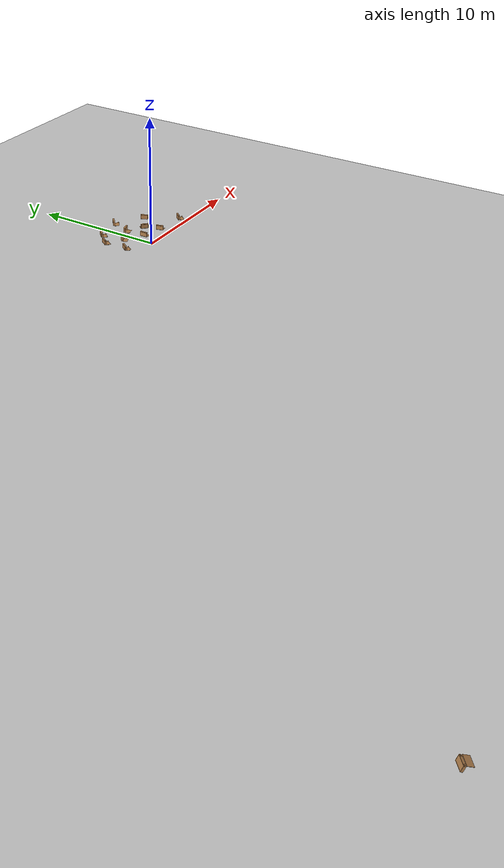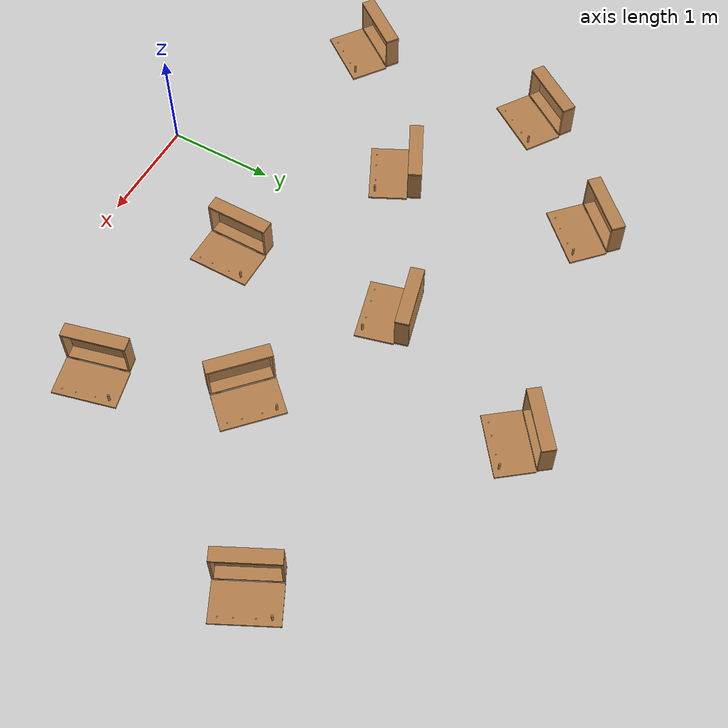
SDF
<sdf version="1.7">
 <world name="default">
  <light name="sun" type="directional">
   <pose>0 0 10 0 -0 0</pose>
   <diffuse>0.8 0.8 0.8 1</diffuse>
   <specular>0.2 0.2 0.2 1</specular>
   <attenuation>
    <range>1000</range>
    <constant>0.9</constant>
    <linear>0.01</linear>
    <quadratic>0.001</quadratic>
   </attenuation>
   <direction>-0.5 0.1 -0.9</direction>
   <spot><inner_angle>0</inner_angle><outer_angle>0</outer_angle><falloff>0</falloff></spot>
  </light>
  <model name="ground_plane">
   <static>1</static>
   <link name="link">
    <collision name="collision">
     <geometry><plane><normal>0 0 1</normal><size>100 100</size></plane></geometry>
     <surface><friction><ode><mu>100</mu><mu2>50</mu2></ode></friction></surface>
    </collision>
    <visual name="visual">
     <cast_shadows>0</cast_shadows>
     <geometry><plane><normal>0 0 1</normal><size>100 100</size></plane></geometry>
     <material>
      <script><uri>file://media/materials/scripts/gazebo.material</uri><name>Gazebo/Grey</name></script>
     </material>
    </visual>
   </link>
  </model>
  <gravity>0 0 -9.8</gravity>
  <magnetic_field>6e-06 2.3e-05 -4.2e-05</magnetic_field>
  <atmosphere type="adiabatic"/>
  <physics type="ode">
   <max_step_size>0.001</max_step_size>
   <enable>0</enable>
   <real_time_factor>1</real_time_factor>
   <real_time_update_rate>1000</real_time_update_rate>
  </physics>
  <scene><ambient>0.4 0.4 0.4 1</ambient><background>0.7 0.7 0.7 1</background><shadows>1</shadows></scene>
  <spherical_coordinates>
   <surface_model>EARTH_WGS84</surface_model>
   <latitude_deg>0</latitude_deg>
   <longitude_deg>0</longitude_deg>
   <elevation>0</elevation>
   <heading_deg>0</heading_deg>
  </spherical_coordinates>
  <model name="b11">
   <static>1</static>
   <frame name="wooden_case::__model__" attached_to="wooden_case::base">
    <pose relative_to="__model__">0 0 0 0 -0 0</pose>
   </frame>
   <link name="wooden_case::base">
    <pose relative_to="wooden_case::__model__">0 0 0.024 0 -0 0</pose>
    <inertial>
     <pose>-0.022184 0 0.171592 0 -0 0</pose>
     <mass>3.96264</mass>
     <inertia>
      <ixx>0.213536</ixx>
      <ixy>0</ixy>
      <ixz>0.000779377</ixz>
      <iyy>0.0708943</iyy>
      <iyz>0</iyz>
      <izz>0.154604</izz>
     </inertia>
    </inertial>
    <collision name="collision_back">
     <pose>-0.053975 0 0.1778 0 -0 0</pose>
     <geometry><box><size>0.01905 0.5461 0.3175</size></box></geometry>
     <surface>
      <contact>
       <poissons_ratio>0.347</poissons_ratio>
       <elastic_modulus>8.8e+09</elastic_modulus>
       <ode><kp>100000</kp><kd>100</kd><max_vel>100</max_vel><min_depth>0.001</min_depth></ode>
      </contact>
      <friction>
       <torsional>
        <coefficient>1</coefficient>
        <use_patch_radius>0</use_patch_radius>
        <surface_radius>0.01</surface_radius>
       </torsional>
      </friction>
     </surface>
    </collision>
    <visual name="visual_back">
     <pose>-0.053975 0 0.1778 0 -0 0</pose>
     <geometry><box><size>0.01905 0.5461 0.3175</size></box></geometry>
     <material>
      <script><uri>file://media/materials/scripts/gazebo.material</uri><name>Gazebo/Wood</name></script>
     </material>
    </visual>
    <collision name="collision_bottom">
     <pose>0 0 0.009525 0 -0 0</pose>
     <geometry><box><size>0.127 0.5842 0.01905</size></box></geometry>
     <surface>
      <contact>
       <poissons_ratio>0.347</poissons_ratio>
       <elastic_modulus>8.8e+09</elastic_modulus>
       <ode><kp>100000</kp><kd>100</kd><max_vel>100</max_vel><min_depth>0.001</min_depth></ode>
      </contact>
      <friction>
       <torsional>
        <coefficient>1</coefficient>
        <use_patch_radius>0</use_patch_radius>
        <surface_radius>0.01</surface_radius>
       </torsional>
      </friction>
     </surface>
    </collision>
    <visual name="visual_bottom">
     <pose>0 0 0.009525 0 -0 0</pose>
     <geometry><box><size>0.127 0.5842 0.01905</size></box></geometry>
     <material>
      <script><uri>file://media/materials/scripts/gazebo.material</uri><name>Gazebo/Wood</name></script>
     </material>
    </visual>
    <collision name="collision_top">
     <pose>0 0 0.346075 0 -0 0</pose>
     <geometry><box><size>0.127 0.5842 0.01905</size></box></geometry>
     <surface>
      <contact>
       <poissons_ratio>0.347</poissons_ratio>
       <elastic_modulus>8.8e+09</elastic_modulus>
       <ode><kp>100000</kp><kd>100</kd><max_vel>100</max_vel><min_depth>0.001</min_depth></ode>
      </contact>
      <friction>
       <torsional>
        <coefficient>1</coefficient>
        <use_patch_radius>0</use_patch_radius>
        <surface_radius>0.01</surface_radius>
       </torsional>
      </friction>
     </surface>
    </collision>
    <visual name="visual_top">
     <pose>0 0 0.346075 0 -0 0</pose>
     <geometry><box><size>0.127 0.5842 0.01905</size></box></geometry>
     <material>
      <script><uri>file://media/materials/scripts/gazebo.material</uri><name>Gazebo/Wood</name></script>
     </material>
    </visual>
    <collision name="collision_left">
     <pose>0 -0.282575 0.1778 0 -0 0</pose>
     <geometry><box><size>0.127 0.01905 0.3175</size></box></geometry>
     <surface>
      <contact>
       <poissons_ratio>0.347</poissons_ratio>
       <elastic_modulus>8.8e+09</elastic_modulus>
       <ode><kp>100000</kp><kd>100</kd><max_vel>100</max_vel><min_depth>0.001</min_depth></ode>
      </contact>
      <friction>
       <torsional>
        <coefficient>1</coefficient>
        <use_patch_radius>0</use_patch_radius>
        <surface_radius>0.01</surface_radius>
       </torsional>
      </friction>
     </surface>
    </collision>
    <visual name="visual_left">
     <pose>0 -0.282575 0.1778 0 -0 0</pose>
     <geometry><box><size>0.127 0.01905 0.3175</size></box></geometry>
     <material>
      <script><uri>file://media/materials/scripts/gazebo.material</uri><name>Gazebo/Wood</name></script>
     </material>
    </visual>
    <collision name="collision_right">
     <pose>0 0.282575 0.1778 0 -0 0</pose>
     <geometry><box><size>0.127 0.01905 0.3175</size></box></geometry>
     <surface>
      <contact>
       <poissons_ratio>0.347</poissons_ratio>
       <elastic_modulus>8.8e+09</elastic_modulus>
       <ode><kp>100000</kp><kd>100</kd><max_vel>100</max_vel><min_depth>0.001</min_depth></ode>
      </contact>
      <friction>
       <torsional>
        <coefficient>1</coefficient>
        <use_patch_radius>0</use_patch_radius>
        <surface_radius>0.01</surface_radius>
       </torsional>
      </friction>
     </surface>
    </collision>
    <visual name="visual_right">
     <pose>0 0.282575 0.1778 0 -0 0</pose>
     <geometry><box><size>0.127 0.01905 0.3175</size></box></geometry>
     <material>
      <script><uri>file://media/materials/scripts/gazebo.material</uri><name>Gazebo/Wood</name></script>
     </material>
    </visual>
    <collision name="collision_block_left">
     <pose>0.0095 -0.2151 -0.012 0 -0 0</pose>
     <geometry><box><size>0.108 0.05 0.024</size></box></geometry>
     <surface>
      <contact>
       <poissons_ratio>0.347</poissons_ratio>
       <elastic_modulus>8.8e+09</elastic_modulus>
       <ode><kp>100000</kp><kd>100</kd><max_vel>100</max_vel><min_depth>0.001</min_depth></ode>
      </contact>
      <friction>
       <torsional>
        <coefficient>1</coefficient>
        <use_patch_radius>0</use_patch_radius>
        <surface_radius>0.01</surface_radius>
       </torsional>
      </friction>
     </surface>
    </collision>
    <visual name="visual_block_left">
     <pose>0.0095 -0.2151 -0.012 0 -0 0</pose>
     <geometry><box><size>0.108 0.05 0.024</size></box></geometry>
     <material>
      <script><uri>file://media/materials/scripts/gazebo.material</uri><name>Gazebo/Wood</name></script>
     </material>
    </visual>
    <collision name="collision_block_right">
     <pose>0.0095 0.2151 -0.012 0 -0 0</pose>
     <geometry><box><size>0.108 0.05 0.024</size></box></geometry>
     <surface>
      <contact>
       <poissons_ratio>0.347</poissons_ratio>
       <elastic_modulus>8.8e+09</elastic_modulus>
       <ode><kp>100000</kp><kd>100</kd><max_vel>100</max_vel><min_depth>0.001</min_depth></ode>
      </contact>
      <friction>
       <torsional>
        <coefficient>1</coefficient>
        <use_patch_radius>0</use_patch_radius>
        <surface_radius>0.01</surface_radius>
       </torsional>
      </friction>
     </surface>
    </collision>
    <visual name="visual_block_right">
     <pose>0.0095 0.2151 -0.012 0 -0 0</pose>
     <geometry><box><size>0.108 0.05 0.024</size></box></geometry>
     <material>
      <script><uri>file://media/materials/scripts/gazebo.material</uri><name>Gazebo/Wood</name></script>
     </material>
    </visual>
   </link>
   <link name="wooden_case::lid">
    <pose relative_to="wooden_case::__model__">0.243775 0 0.009525 0 -0 0</pose>
    <inertial>
     <mass>1.97874</mass>
     <inertia>
      <ixx>0.0563367</ixx>
      <ixy>0</ixy>
      <ixz>0</ixz>
      <iyy>0.020911</iyy>
      <iyz>0</iyz>
      <izz>0.0771281</izz>
     </inertia>
    </inertial>
    <collision name="collision">
     <geometry><box><size>0.3556 0.5842 0.01905</size></box></geometry>
     <surface>
      <contact>
       <poissons_ratio>0.347</poissons_ratio>
       <elastic_modulus>8.8e+09</elastic_modulus>
       <ode><kp>100000</kp><kd>100</kd><max_vel>100</max_vel><min_depth>0.001</min_depth></ode>
      </contact>
      <friction>
       <torsional>
        <coefficient>1</coefficient>
        <use_patch_radius>0</use_patch_radius>
        <surface_radius>0.01</surface_radius>
       </torsional>
      </friction>
     </surface>
    </collision>
    <visual name="visual">
     <geometry><box><size>0.3556 0.5842 0.01905</size></box></geometry>
     <material>
      <script><uri>file://media/materials/scripts/gazebo.material</uri><name>Gazebo/Wood</name></script>
     </material>
    </visual>
    <visual name="tee_nut_1">
     <pose>0.122 -0.216 0 0 -0 0</pose>
     <geometry><cylinder><radius>0.00635</radius><length>0.0192405</length></cylinder></geometry>
     <material>
      <script><uri>file://media/materials/scripts/gazebo.material</uri><name>Gazebo/Grey</name></script>
     </material>
    </visual>
    <visual name="tee_nut_2">
     <pose>0.122 -0.088 0 0 -0 0</pose>
     <geometry><cylinder><radius>0.00635</radius><length>0.0192405</length></cylinder></geometry>
     <material>
      <script><uri>file://media/materials/scripts/gazebo.material</uri><name>Gazebo/Grey</name></script>
     </material>
    </visual>
    <visual name="tee_nut_3">
     <pose>0.122 0.088 0 0 -0 0</pose>
     <geometry><cylinder><radius>0.00635</radius><length>0.0192405</length></cylinder></geometry>
     <material>
      <script><uri>file://media/materials/scripts/gazebo.material</uri><name>Gazebo/Grey</name></script>
     </material>
    </visual>
    <visual name="tee_nut_4">
     <pose>0.122 0.216 0 0 -0 0</pose>
     <geometry><cylinder><radius>0.00635</radius><length>0.0192405</length></cylinder></geometry>
     <material>
      <script><uri>file://media/materials/scripts/gazebo.material</uri><name>Gazebo/Grey</name></script>
     </material>
    </visual>
   </link>
   <joint name="wooden_case::lid_hinge" type="revolute">
    <pose>-0.1778 0 0.01905 0 -0 0</pose>
    <parent>wooden_case::base</parent>
    <child>wooden_case::lid</child>
    <axis>
     <xyz>0 1 0</xyz>
     <limit><upper>0.523599</upper><lower>-1.5708</lower></limit>
     <dynamics><spring_reference>0</spring_reference><spring_stiffness>0</spring_stiffness></dynamics>
    </axis>
   </joint>
   <frame name="peg::__model__" attached_to="peg::link">
    <pose relative_to="__model__">0.365774 0.216 0.01905 0 -0 0</pose>
   </frame>
   <link name="peg::link">
    <pose relative_to="peg::__model__">0 0 0.04 0 -0 0</pose>
    <inertial>
     <mass>0.0175</mass>
     <inertia>
      <ixx>9.74923e-06</ixx>
      <ixy>0</ixy>
      <ixz>0</ixz>
      <iyy>9.74923e-06</iyy>
      <iyz>0</iyz>
      <izz>8.31797e-07</izz>
     </inertia>
    </inertial>
    <collision name="collision">
     <geometry><cylinder><radius>0.00975</radius><length>0.08</length></cylinder></geometry>
     <surface>
      <contact>
       <poissons_ratio>0.347</poissons_ratio>
       <elastic_modulus>8.8e+09</elastic_modulus>
       <ode><kp>100000</kp><kd>100</kd><max_vel>100</max_vel><min_depth>0.001</min_depth></ode>
      </contact>
      <friction>
       <torsional>
        <coefficient>1</coefficient>
        <use_patch_radius>0</use_patch_radius>
        <surface_radius>0.01</surface_radius>
       </torsional>
      </friction>
     </surface>
    </collision>
    <visual name="visual">
     <geometry><cylinder><radius>0.00975</radius><length>0.08</length></cylinder></geometry>
     <material>
      <script><uri>file://media/materials/scripts/gazebo.material</uri><name>Gazebo/Wood</name></script>
     </material>
    </visual>
   </link>
   <joint name="case_peg" type="revolute">
    <child>peg::link</child>
    <parent>wooden_case::lid</parent>
    <axis>
     <xyz>0 0 1</xyz>
     <limit><upper>0</upper><lower>0</lower></limit>
     <dynamics><spring_reference>0</spring_reference><spring_stiffness>0</spring_stiffness></dynamics>
    </axis>
   </joint>
   <pose>0.735733 1.20815 -0.001057 -1e-06 -0.000428 0</pose>
  </model>
  <model name="b10">
   <static>1</static>
   <frame name="wooden_case::__model__" attached_to="wooden_case::base">
    <pose relative_to="__model__">0 0 0 0 -0 0</pose>
   </frame>
   <link name="wooden_case::base">
    <pose relative_to="wooden_case::__model__">0 0 0.024 0 -0 0</pose>
    <inertial>
     <pose>-0.022184 0 0.171592 0 -0 0</pose>
     <mass>3.96264</mass>
     <inertia>
      <ixx>0.213536</ixx>
      <ixy>0</ixy>
      <ixz>0.000779377</ixz>
      <iyy>0.0708943</iyy>
      <iyz>0</iyz>
      <izz>0.154604</izz>
     </inertia>
    </inertial>
    <collision name="collision_back">
     <pose>-0.053975 0 0.1778 0 -0 0</pose>
     <geometry><box><size>0.01905 0.5461 0.3175</size></box></geometry>
     <surface>
      <contact>
       <poissons_ratio>0.347</poissons_ratio>
       <elastic_modulus>8.8e+09</elastic_modulus>
       <ode><kp>100000</kp><kd>100</kd><max_vel>100</max_vel><min_depth>0.001</min_depth></ode>
      </contact>
      <friction>
       <torsional>
        <coefficient>1</coefficient>
        <use_patch_radius>0</use_patch_radius>
        <surface_radius>0.01</surface_radius>
       </torsional>
      </friction>
     </surface>
    </collision>
    <visual name="visual_back">
     <pose>-0.053975 0 0.1778 0 -0 0</pose>
     <geometry><box><size>0.01905 0.5461 0.3175</size></box></geometry>
     <material>
      <script><uri>file://media/materials/scripts/gazebo.material</uri><name>Gazebo/Wood</name></script>
     </material>
    </visual>
    <collision name="collision_bottom">
     <pose>0 0 0.009525 0 -0 0</pose>
     <geometry><box><size>0.127 0.5842 0.01905</size></box></geometry>
     <surface>
      <contact>
       <poissons_ratio>0.347</poissons_ratio>
       <elastic_modulus>8.8e+09</elastic_modulus>
       <ode><kp>100000</kp><kd>100</kd><max_vel>100</max_vel><min_depth>0.001</min_depth></ode>
      </contact>
      <friction>
       <torsional>
        <coefficient>1</coefficient>
        <use_patch_radius>0</use_patch_radius>
        <surface_radius>0.01</surface_radius>
       </torsional>
      </friction>
     </surface>
    </collision>
    <visual name="visual_bottom">
     <pose>0 0 0.009525 0 -0 0</pose>
     <geometry><box><size>0.127 0.5842 0.01905</size></box></geometry>
     <material>
      <script><uri>file://media/materials/scripts/gazebo.material</uri><name>Gazebo/Wood</name></script>
     </material>
    </visual>
    <collision name="collision_top">
     <pose>0 0 0.346075 0 -0 0</pose>
     <geometry><box><size>0.127 0.5842 0.01905</size></box></geometry>
     <surface>
      <contact>
       <poissons_ratio>0.347</poissons_ratio>
       <elastic_modulus>8.8e+09</elastic_modulus>
       <ode><kp>100000</kp><kd>100</kd><max_vel>100</max_vel><min_depth>0.001</min_depth></ode>
      </contact>
      <friction>
       <torsional>
        <coefficient>1</coefficient>
        <use_patch_radius>0</use_patch_radius>
        <surface_radius>0.01</surface_radius>
       </torsional>
      </friction>
     </surface>
    </collision>
    <visual name="visual_top">
     <pose>0 0 0.346075 0 -0 0</pose>
     <geometry><box><size>0.127 0.5842 0.01905</size></box></geometry>
     <material>
      <script><uri>file://media/materials/scripts/gazebo.material</uri><name>Gazebo/Wood</name></script>
     </material>
    </visual>
    <collision name="collision_left">
     <pose>0 -0.282575 0.1778 0 -0 0</pose>
     <geometry><box><size>0.127 0.01905 0.3175</size></box></geometry>
     <surface>
      <contact>
       <poissons_ratio>0.347</poissons_ratio>
       <elastic_modulus>8.8e+09</elastic_modulus>
       <ode><kp>100000</kp><kd>100</kd><max_vel>100</max_vel><min_depth>0.001</min_depth></ode>
      </contact>
      <friction>
       <torsional>
        <coefficient>1</coefficient>
        <use_patch_radius>0</use_patch_radius>
        <surface_radius>0.01</surface_radius>
       </torsional>
      </friction>
     </surface>
    </collision>
    <visual name="visual_left">
     <pose>0 -0.282575 0.1778 0 -0 0</pose>
     <geometry><box><size>0.127 0.01905 0.3175</size></box></geometry>
     <material>
      <script><uri>file://media/materials/scripts/gazebo.material</uri><name>Gazebo/Wood</name></script>
     </material>
    </visual>
    <collision name="collision_right">
     <pose>0 0.282575 0.1778 0 -0 0</pose>
     <geometry><box><size>0.127 0.01905 0.3175</size></box></geometry>
     <surface>
      <contact>
       <poissons_ratio>0.347</poissons_ratio>
       <elastic_modulus>8.8e+09</elastic_modulus>
       <ode><kp>100000</kp><kd>100</kd><max_vel>100</max_vel><min_depth>0.001</min_depth></ode>
      </contact>
      <friction>
       <torsional>
        <coefficient>1</coefficient>
        <use_patch_radius>0</use_patch_radius>
        <surface_radius>0.01</surface_radius>
       </torsional>
      </friction>
     </surface>
    </collision>
    <visual name="visual_right">
     <pose>0 0.282575 0.1778 0 -0 0</pose>
     <geometry><box><size>0.127 0.01905 0.3175</size></box></geometry>
     <material>
      <script><uri>file://media/materials/scripts/gazebo.material</uri><name>Gazebo/Wood</name></script>
     </material>
    </visual>
    <collision name="collision_block_left">
     <pose>0.0095 -0.2151 -0.012 0 -0 0</pose>
     <geometry><box><size>0.108 0.05 0.024</size></box></geometry>
     <surface>
      <contact>
       <poissons_ratio>0.347</poissons_ratio>
       <elastic_modulus>8.8e+09</elastic_modulus>
       <ode><kp>100000</kp><kd>100</kd><max_vel>100</max_vel><min_depth>0.001</min_depth></ode>
      </contact>
      <friction>
       <torsional>
        <coefficient>1</coefficient>
        <use_patch_radius>0</use_patch_radius>
        <surface_radius>0.01</surface_radius>
       </torsional>
      </friction>
     </surface>
    </collision>
    <visual name="visual_block_left">
     <pose>0.0095 -0.2151 -0.012 0 -0 0</pose>
     <geometry><box><size>0.108 0.05 0.024</size></box></geometry>
     <material>
      <script><uri>file://media/materials/scripts/gazebo.material</uri><name>Gazebo/Wood</name></script>
     </material>
    </visual>
    <collision name="collision_block_right">
     <pose>0.0095 0.2151 -0.012 0 -0 0</pose>
     <geometry><box><size>0.108 0.05 0.024</size></box></geometry>
     <surface>
      <contact>
       <poissons_ratio>0.347</poissons_ratio>
       <elastic_modulus>8.8e+09</elastic_modulus>
       <ode><kp>100000</kp><kd>100</kd><max_vel>100</max_vel><min_depth>0.001</min_depth></ode>
      </contact>
      <friction>
       <torsional>
        <coefficient>1</coefficient>
        <use_patch_radius>0</use_patch_radius>
        <surface_radius>0.01</surface_radius>
       </torsional>
      </friction>
     </surface>
    </collision>
    <visual name="visual_block_right">
     <pose>0.0095 0.2151 -0.012 0 -0 0</pose>
     <geometry><box><size>0.108 0.05 0.024</size></box></geometry>
     <material>
      <script><uri>file://media/materials/scripts/gazebo.material</uri><name>Gazebo/Wood</name></script>
     </material>
    </visual>
   </link>
   <link name="wooden_case::lid">
    <pose relative_to="wooden_case::__model__">0.243775 0 0.009525 0 -0 0</pose>
    <inertial>
     <mass>1.97874</mass>
     <inertia>
      <ixx>0.0563367</ixx>
      <ixy>0</ixy>
      <ixz>0</ixz>
      <iyy>0.020911</iyy>
      <iyz>0</iyz>
      <izz>0.0771281</izz>
     </inertia>
    </inertial>
    <collision name="collision">
     <geometry><box><size>0.3556 0.5842 0.01905</size></box></geometry>
     <surface>
      <contact>
       <poissons_ratio>0.347</poissons_ratio>
       <elastic_modulus>8.8e+09</elastic_modulus>
       <ode><kp>100000</kp><kd>100</kd><max_vel>100</max_vel><min_depth>0.001</min_depth></ode>
      </contact>
      <friction>
       <torsional>
        <coefficient>1</coefficient>
        <use_patch_radius>0</use_patch_radius>
        <surface_radius>0.01</surface_radius>
       </torsional>
      </friction>
     </surface>
    </collision>
    <visual name="visual">
     <geometry><box><size>0.3556 0.5842 0.01905</size></box></geometry>
     <material>
      <script><uri>file://media/materials/scripts/gazebo.material</uri><name>Gazebo/Wood</name></script>
     </material>
    </visual>
    <visual name="tee_nut_1">
     <pose>0.122 -0.216 0 0 -0 0</pose>
     <geometry><cylinder><radius>0.00635</radius><length>0.0192405</length></cylinder></geometry>
     <material>
      <script><uri>file://media/materials/scripts/gazebo.material</uri><name>Gazebo/Grey</name></script>
     </material>
    </visual>
    <visual name="tee_nut_2">
     <pose>0.122 -0.088 0 0 -0 0</pose>
     <geometry><cylinder><radius>0.00635</radius><length>0.0192405</length></cylinder></geometry>
     <material>
      <script><uri>file://media/materials/scripts/gazebo.material</uri><name>Gazebo/Grey</name></script>
     </material>
    </visual>
    <visual name="tee_nut_3">
     <pose>0.122 0.088 0 0 -0 0</pose>
     <geometry><cylinder><radius>0.00635</radius><length>0.0192405</length></cylinder></geometry>
     <material>
      <script><uri>file://media/materials/scripts/gazebo.material</uri><name>Gazebo/Grey</name></script>
     </material>
    </visual>
    <visual name="tee_nut_4">
     <pose>0.122 0.216 0 0 -0 0</pose>
     <geometry><cylinder><radius>0.00635</radius><length>0.0192405</length></cylinder></geometry>
     <material>
      <script><uri>file://media/materials/scripts/gazebo.material</uri><name>Gazebo/Grey</name></script>
     </material>
    </visual>
   </link>
   <joint name="wooden_case::lid_hinge" type="revolute">
    <pose>-0.1778 0 0.01905 0 -0 0</pose>
    <parent>wooden_case::base</parent>
    <child>wooden_case::lid</child>
    <axis>
     <xyz>0 1 0</xyz>
     <limit><upper>0.523599</upper><lower>-1.5708</lower></limit>
     <dynamics><spring_reference>0</spring_reference><spring_stiffness>0</spring_stiffness></dynamics>
    </axis>
   </joint>
   <frame name="peg::__model__" attached_to="peg::link">
    <pose relative_to="__model__">0.365774 0.216 0.01905 0 -0 0</pose>
   </frame>
   <link name="peg::link">
    <pose relative_to="peg::__model__">0 0 0.04 0 -0 0</pose>
    <inertial>
     <mass>0.0175</mass>
     <inertia>
      <ixx>9.74923e-06</ixx>
      <ixy>0</ixy>
      <ixz>0</ixz>
      <iyy>9.74923e-06</iyy>
      <iyz>0</iyz>
      <izz>8.31797e-07</izz>
     </inertia>
    </inertial>
    <collision name="collision">
     <geometry><cylinder><radius>0.00975</radius><length>0.08</length></cylinder></geometry>
     <surface>
      <contact>
       <poissons_ratio>0.347</poissons_ratio>
       <elastic_modulus>8.8e+09</elastic_modulus>
       <ode><kp>100000</kp><kd>100</kd><max_vel>100</max_vel><min_depth>0.001</min_depth></ode>
      </contact>
      <friction>
       <torsional>
        <coefficient>1</coefficient>
        <use_patch_radius>0</use_patch_radius>
        <surface_radius>0.01</surface_radius>
       </torsional>
      </friction>
     </surface>
    </collision>
    <visual name="visual">
     <geometry><cylinder><radius>0.00975</radius><length>0.08</length></cylinder></geometry>
     <material>
      <script><uri>file://media/materials/scripts/gazebo.material</uri><name>Gazebo/Wood</name></script>
     </material>
    </visual>
   </link>
   <joint name="case_peg" type="revolute">
    <child>peg::link</child>
    <parent>wooden_case::lid</parent>
    <axis>
     <xyz>0 0 1</xyz>
     <limit><upper>0</upper><lower>0</lower></limit>
     <dynamics><spring_reference>0</spring_reference><spring_stiffness>0</spring_stiffness></dynamics>
    </axis>
   </joint>
   <pose>-1.96191 1.13258 -0.001057 -0 -0.00042 -0.631587</pose>
  </model>
  <model name="b9">
   <static>1</static>
   <frame name="wooden_case::__model__" attached_to="wooden_case::base">
    <pose relative_to="__model__">0 0 0 0 -0 0</pose>
   </frame>
   <link name="wooden_case::base">
    <pose relative_to="wooden_case::__model__">0 0 0.024 0 -0 0</pose>
    <inertial>
     <pose>-0.022184 0 0.171592 0 -0 0</pose>
     <mass>3.96264</mass>
     <inertia>
      <ixx>0.213536</ixx>
      <ixy>0</ixy>
      <ixz>0.000779377</ixz>
      <iyy>0.0708943</iyy>
      <iyz>0</iyz>
      <izz>0.154604</izz>
     </inertia>
    </inertial>
    <collision name="collision_back">
     <pose>-0.053975 0 0.1778 0 -0 0</pose>
     <geometry><box><size>0.01905 0.5461 0.3175</size></box></geometry>
     <surface>
      <contact>
       <poissons_ratio>0.347</poissons_ratio>
       <elastic_modulus>8.8e+09</elastic_modulus>
       <ode><kp>100000</kp><kd>100</kd><max_vel>100</max_vel><min_depth>0.001</min_depth></ode>
      </contact>
      <friction>
       <torsional>
        <coefficient>1</coefficient>
        <use_patch_radius>0</use_patch_radius>
        <surface_radius>0.01</surface_radius>
       </torsional>
      </friction>
     </surface>
    </collision>
    <visual name="visual_back">
     <pose>-0.053975 0 0.1778 0 -0 0</pose>
     <geometry><box><size>0.01905 0.5461 0.3175</size></box></geometry>
     <material>
      <script><uri>file://media/materials/scripts/gazebo.material</uri><name>Gazebo/Wood</name></script>
     </material>
    </visual>
    <collision name="collision_bottom">
     <pose>0 0 0.009525 0 -0 0</pose>
     <geometry><box><size>0.127 0.5842 0.01905</size></box></geometry>
     <surface>
      <contact>
       <poissons_ratio>0.347</poissons_ratio>
       <elastic_modulus>8.8e+09</elastic_modulus>
       <ode><kp>100000</kp><kd>100</kd><max_vel>100</max_vel><min_depth>0.001</min_depth></ode>
      </contact>
      <friction>
       <torsional>
        <coefficient>1</coefficient>
        <use_patch_radius>0</use_patch_radius>
        <surface_radius>0.01</surface_radius>
       </torsional>
      </friction>
     </surface>
    </collision>
    <visual name="visual_bottom">
     <pose>0 0 0.009525 0 -0 0</pose>
     <geometry><box><size>0.127 0.5842 0.01905</size></box></geometry>
     <material>
      <script><uri>file://media/materials/scripts/gazebo.material</uri><name>Gazebo/Wood</name></script>
     </material>
    </visual>
    <collision name="collision_top">
     <pose>0 0 0.346075 0 -0 0</pose>
     <geometry><box><size>0.127 0.5842 0.01905</size></box></geometry>
     <surface>
      <contact>
       <poissons_ratio>0.347</poissons_ratio>
       <elastic_modulus>8.8e+09</elastic_modulus>
       <ode><kp>100000</kp><kd>100</kd><max_vel>100</max_vel><min_depth>0.001</min_depth></ode>
      </contact>
      <friction>
       <torsional>
        <coefficient>1</coefficient>
        <use_patch_radius>0</use_patch_radius>
        <surface_radius>0.01</surface_radius>
       </torsional>
      </friction>
     </surface>
    </collision>
    <visual name="visual_top">
     <pose>0 0 0.346075 0 -0 0</pose>
     <geometry><box><size>0.127 0.5842 0.01905</size></box></geometry>
     <material>
      <script><uri>file://media/materials/scripts/gazebo.material</uri><name>Gazebo/Wood</name></script>
     </material>
    </visual>
    <collision name="collision_left">
     <pose>0 -0.282575 0.1778 0 -0 0</pose>
     <geometry><box><size>0.127 0.01905 0.3175</size></box></geometry>
     <surface>
      <contact>
       <poissons_ratio>0.347</poissons_ratio>
       <elastic_modulus>8.8e+09</elastic_modulus>
       <ode><kp>100000</kp><kd>100</kd><max_vel>100</max_vel><min_depth>0.001</min_depth></ode>
      </contact>
      <friction>
       <torsional>
        <coefficient>1</coefficient>
        <use_patch_radius>0</use_patch_radius>
        <surface_radius>0.01</surface_radius>
       </torsional>
      </friction>
     </surface>
    </collision>
    <visual name="visual_left">
     <pose>0 -0.282575 0.1778 0 -0 0</pose>
     <geometry><box><size>0.127 0.01905 0.3175</size></box></geometry>
     <material>
      <script><uri>file://media/materials/scripts/gazebo.material</uri><name>Gazebo/Wood</name></script>
     </material>
    </visual>
    <collision name="collision_right">
     <pose>0 0.282575 0.1778 0 -0 0</pose>
     <geometry><box><size>0.127 0.01905 0.3175</size></box></geometry>
     <surface>
      <contact>
       <poissons_ratio>0.347</poissons_ratio>
       <elastic_modulus>8.8e+09</elastic_modulus>
       <ode><kp>100000</kp><kd>100</kd><max_vel>100</max_vel><min_depth>0.001</min_depth></ode>
      </contact>
      <friction>
       <torsional>
        <coefficient>1</coefficient>
        <use_patch_radius>0</use_patch_radius>
        <surface_radius>0.01</surface_radius>
       </torsional>
      </friction>
     </surface>
    </collision>
    <visual name="visual_right">
     <pose>0 0.282575 0.1778 0 -0 0</pose>
     <geometry><box><size>0.127 0.01905 0.3175</size></box></geometry>
     <material>
      <script><uri>file://media/materials/scripts/gazebo.material</uri><name>Gazebo/Wood</name></script>
     </material>
    </visual>
    <collision name="collision_block_left">
     <pose>0.0095 -0.2151 -0.012 0 -0 0</pose>
     <geometry><box><size>0.108 0.05 0.024</size></box></geometry>
     <surface>
      <contact>
       <poissons_ratio>0.347</poissons_ratio>
       <elastic_modulus>8.8e+09</elastic_modulus>
       <ode><kp>100000</kp><kd>100</kd><max_vel>100</max_vel><min_depth>0.001</min_depth></ode>
      </contact>
      <friction>
       <torsional>
        <coefficient>1</coefficient>
        <use_patch_radius>0</use_patch_radius>
        <surface_radius>0.01</surface_radius>
       </torsional>
      </friction>
     </surface>
    </collision>
    <visual name="visual_block_left">
     <pose>0.0095 -0.2151 -0.012 0 -0 0</pose>
     <geometry><box><size>0.108 0.05 0.024</size></box></geometry>
     <material>
      <script><uri>file://media/materials/scripts/gazebo.material</uri><name>Gazebo/Wood</name></script>
     </material>
    </visual>
    <collision name="collision_block_right">
     <pose>0.0095 0.2151 -0.012 0 -0 0</pose>
     <geometry><box><size>0.108 0.05 0.024</size></box></geometry>
     <surface>
      <contact>
       <poissons_ratio>0.347</poissons_ratio>
       <elastic_modulus>8.8e+09</elastic_modulus>
       <ode><kp>100000</kp><kd>100</kd><max_vel>100</max_vel><min_depth>0.001</min_depth></ode>
      </contact>
      <friction>
       <torsional>
        <coefficient>1</coefficient>
        <use_patch_radius>0</use_patch_radius>
        <surface_radius>0.01</surface_radius>
       </torsional>
      </friction>
     </surface>
    </collision>
    <visual name="visual_block_right">
     <pose>0.0095 0.2151 -0.012 0 -0 0</pose>
     <geometry><box><size>0.108 0.05 0.024</size></box></geometry>
     <material>
      <script><uri>file://media/materials/scripts/gazebo.material</uri><name>Gazebo/Wood</name></script>
     </material>
    </visual>
   </link>
   <link name="wooden_case::lid">
    <pose relative_to="wooden_case::__model__">0.243775 0 0.009525 0 -0 0</pose>
    <inertial>
     <mass>1.97874</mass>
     <inertia>
      <ixx>0.0563367</ixx>
      <ixy>0</ixy>
      <ixz>0</ixz>
      <iyy>0.020911</iyy>
      <iyz>0</iyz>
      <izz>0.0771281</izz>
     </inertia>
    </inertial>
    <collision name="collision">
     <geometry><box><size>0.3556 0.5842 0.01905</size></box></geometry>
     <surface>
      <contact>
       <poissons_ratio>0.347</poissons_ratio>
       <elastic_modulus>8.8e+09</elastic_modulus>
       <ode><kp>100000</kp><kd>100</kd><max_vel>100</max_vel><min_depth>0.001</min_depth></ode>
      </contact>
      <friction>
       <torsional>
        <coefficient>1</coefficient>
        <use_patch_radius>0</use_patch_radius>
        <surface_radius>0.01</surface_radius>
       </torsional>
      </friction>
     </surface>
    </collision>
    <visual name="visual">
     <geometry><box><size>0.3556 0.5842 0.01905</size></box></geometry>
     <material>
      <script><uri>file://media/materials/scripts/gazebo.material</uri><name>Gazebo/Wood</name></script>
     </material>
    </visual>
    <visual name="tee_nut_1">
     <pose>0.122 -0.216 0 0 -0 0</pose>
     <geometry><cylinder><radius>0.00635</radius><length>0.0192405</length></cylinder></geometry>
     <material>
      <script><uri>file://media/materials/scripts/gazebo.material</uri><name>Gazebo/Grey</name></script>
     </material>
    </visual>
    <visual name="tee_nut_2">
     <pose>0.122 -0.088 0 0 -0 0</pose>
     <geometry><cylinder><radius>0.00635</radius><length>0.0192405</length></cylinder></geometry>
     <material>
      <script><uri>file://media/materials/scripts/gazebo.material</uri><name>Gazebo/Grey</name></script>
     </material>
    </visual>
    <visual name="tee_nut_3">
     <pose>0.122 0.088 0 0 -0 0</pose>
     <geometry><cylinder><radius>0.00635</radius><length>0.0192405</length></cylinder></geometry>
     <material>
      <script><uri>file://media/materials/scripts/gazebo.material</uri><name>Gazebo/Grey</name></script>
     </material>
    </visual>
    <visual name="tee_nut_4">
     <pose>0.122 0.216 0 0 -0 0</pose>
     <geometry><cylinder><radius>0.00635</radius><length>0.0192405</length></cylinder></geometry>
     <material>
      <script><uri>file://media/materials/scripts/gazebo.material</uri><name>Gazebo/Grey</name></script>
     </material>
    </visual>
   </link>
   <joint name="wooden_case::lid_hinge" type="revolute">
    <pose>-0.1778 0 0.01905 0 -0 0</pose>
    <parent>wooden_case::base</parent>
    <child>wooden_case::lid</child>
    <axis>
     <xyz>0 1 0</xyz>
     <limit><upper>0.523599</upper><lower>-1.5708</lower></limit>
     <dynamics><spring_reference>0</spring_reference><spring_stiffness>0</spring_stiffness></dynamics>
    </axis>
   </joint>
   <frame name="peg::__model__" attached_to="peg::link">
    <pose relative_to="__model__">0.365774 0.216 0.01905 0 -0 0</pose>
   </frame>
   <link name="peg::link">
    <pose relative_to="peg::__model__">0 0 0.04 0 -0 0</pose>
    <inertial>
     <mass>0.0175</mass>
     <inertia>
      <ixx>9.74923e-06</ixx>
      <ixy>0</ixy>
      <ixz>0</ixz>
      <iyy>9.74923e-06</iyy>
      <iyz>0</iyz>
      <izz>8.31797e-07</izz>
     </inertia>
    </inertial>
    <collision name="collision">
     <geometry><cylinder><radius>0.00975</radius><length>0.08</length></cylinder></geometry>
     <surface>
      <contact>
       <poissons_ratio>0.347</poissons_ratio>
       <elastic_modulus>8.8e+09</elastic_modulus>
       <ode><kp>100000</kp><kd>100</kd><max_vel>100</max_vel><min_depth>0.001</min_depth></ode>
      </contact>
      <friction>
       <torsional>
        <coefficient>1</coefficient>
        <use_patch_radius>0</use_patch_radius>
        <surface_radius>0.01</surface_radius>
       </torsional>
      </friction>
     </surface>
    </collision>
    <visual name="visual">
     <geometry><cylinder><radius>0.00975</radius><length>0.08</length></cylinder></geometry>
     <material>
      <script><uri>file://media/materials/scripts/gazebo.material</uri><name>Gazebo/Wood</name></script>
     </material>
    </visual>
   </link>
   <joint name="case_peg" type="revolute">
    <child>peg::link</child>
    <parent>wooden_case::lid</parent>
    <axis>
     <xyz>0 0 1</xyz>
     <limit><upper>0</upper><lower>0</lower></limit>
     <dynamics><spring_reference>0</spring_reference><spring_stiffness>0</spring_stiffness></dynamics>
    </axis>
   </joint>
   <pose>1.26633 4.44379 -0.001057 -1e-06 -0.000422 -0.906076</pose>
  </model>
  <model name="b0">
   <static>1</static>
   <frame name="wooden_case::__model__" attached_to="wooden_case::base">
    <pose relative_to="__model__">0 0 0 0 -0 0</pose>
   </frame>
   <link name="wooden_case::base">
    <pose relative_to="wooden_case::__model__">0 0 0.024 0 -0 0</pose>
    <inertial>
     <pose>-0.022184 0 0.171592 0 -0 0</pose>
     <mass>3.96264</mass>
     <inertia>
      <ixx>0.213536</ixx>
      <ixy>0</ixy>
      <ixz>0.000779377</ixz>
      <iyy>0.0708943</iyy>
      <iyz>0</iyz>
      <izz>0.154604</izz>
     </inertia>
    </inertial>
    <collision name="collision_back">
     <pose>-0.053975 0 0.1778 0 -0 0</pose>
     <geometry><box><size>0.01905 0.5461 0.3175</size></box></geometry>
     <surface>
      <contact>
       <poissons_ratio>0.347</poissons_ratio>
       <elastic_modulus>8.8e+09</elastic_modulus>
       <ode><kp>100000</kp><kd>100</kd><max_vel>100</max_vel><min_depth>0.001</min_depth></ode>
      </contact>
      <friction>
       <torsional>
        <coefficient>1</coefficient>
        <use_patch_radius>0</use_patch_radius>
        <surface_radius>0.01</surface_radius>
       </torsional>
      </friction>
     </surface>
    </collision>
    <visual name="visual_back">
     <pose>-0.053975 0 0.1778 0 -0 0</pose>
     <geometry><box><size>0.01905 0.5461 0.3175</size></box></geometry>
     <material>
      <script><uri>file://media/materials/scripts/gazebo.material</uri><name>Gazebo/Wood</name></script>
     </material>
    </visual>
    <collision name="collision_bottom">
     <pose>0 0 0.009525 0 -0 0</pose>
     <geometry><box><size>0.127 0.5842 0.01905</size></box></geometry>
     <surface>
      <contact>
       <poissons_ratio>0.347</poissons_ratio>
       <elastic_modulus>8.8e+09</elastic_modulus>
       <ode><kp>100000</kp><kd>100</kd><max_vel>100</max_vel><min_depth>0.001</min_depth></ode>
      </contact>
      <friction>
       <torsional>
        <coefficient>1</coefficient>
        <use_patch_radius>0</use_patch_radius>
        <surface_radius>0.01</surface_radius>
       </torsional>
      </friction>
     </surface>
    </collision>
    <visual name="visual_bottom">
     <pose>0 0 0.009525 0 -0 0</pose>
     <geometry><box><size>0.127 0.5842 0.01905</size></box></geometry>
     <material>
      <script><uri>file://media/materials/scripts/gazebo.material</uri><name>Gazebo/Wood</name></script>
     </material>
    </visual>
    <collision name="collision_top">
     <pose>0 0 0.346075 0 -0 0</pose>
     <geometry><box><size>0.127 0.5842 0.01905</size></box></geometry>
     <surface>
      <contact>
       <poissons_ratio>0.347</poissons_ratio>
       <elastic_modulus>8.8e+09</elastic_modulus>
       <ode><kp>100000</kp><kd>100</kd><max_vel>100</max_vel><min_depth>0.001</min_depth></ode>
      </contact>
      <friction>
       <torsional>
        <coefficient>1</coefficient>
        <use_patch_radius>0</use_patch_radius>
        <surface_radius>0.01</surface_radius>
       </torsional>
      </friction>
     </surface>
    </collision>
    <visual name="visual_top">
     <pose>0 0 0.346075 0 -0 0</pose>
     <geometry><box><size>0.127 0.5842 0.01905</size></box></geometry>
     <material>
      <script><uri>file://media/materials/scripts/gazebo.material</uri><name>Gazebo/Wood</name></script>
     </material>
    </visual>
    <collision name="collision_left">
     <pose>0 -0.282575 0.1778 0 -0 0</pose>
     <geometry><box><size>0.127 0.01905 0.3175</size></box></geometry>
     <surface>
      <contact>
       <poissons_ratio>0.347</poissons_ratio>
       <elastic_modulus>8.8e+09</elastic_modulus>
       <ode><kp>100000</kp><kd>100</kd><max_vel>100</max_vel><min_depth>0.001</min_depth></ode>
      </contact>
      <friction>
       <torsional>
        <coefficient>1</coefficient>
        <use_patch_radius>0</use_patch_radius>
        <surface_radius>0.01</surface_radius>
       </torsional>
      </friction>
     </surface>
    </collision>
    <visual name="visual_left">
     <pose>0 -0.282575 0.1778 0 -0 0</pose>
     <geometry><box><size>0.127 0.01905 0.3175</size></box></geometry>
     <material>
      <script><uri>file://media/materials/scripts/gazebo.material</uri><name>Gazebo/Wood</name></script>
     </material>
    </visual>
    <collision name="collision_right">
     <pose>0 0.282575 0.1778 0 -0 0</pose>
     <geometry><box><size>0.127 0.01905 0.3175</size></box></geometry>
     <surface>
      <contact>
       <poissons_ratio>0.347</poissons_ratio>
       <elastic_modulus>8.8e+09</elastic_modulus>
       <ode><kp>100000</kp><kd>100</kd><max_vel>100</max_vel><min_depth>0.001</min_depth></ode>
      </contact>
      <friction>
       <torsional>
        <coefficient>1</coefficient>
        <use_patch_radius>0</use_patch_radius>
        <surface_radius>0.01</surface_radius>
       </torsional>
      </friction>
     </surface>
    </collision>
    <visual name="visual_right">
     <pose>0 0.282575 0.1778 0 -0 0</pose>
     <geometry><box><size>0.127 0.01905 0.3175</size></box></geometry>
     <material>
      <script><uri>file://media/materials/scripts/gazebo.material</uri><name>Gazebo/Wood</name></script>
     </material>
    </visual>
    <collision name="collision_block_left">
     <pose>0.0095 -0.2151 -0.012 0 -0 0</pose>
     <geometry><box><size>0.108 0.05 0.024</size></box></geometry>
     <surface>
      <contact>
       <poissons_ratio>0.347</poissons_ratio>
       <elastic_modulus>8.8e+09</elastic_modulus>
       <ode><kp>100000</kp><kd>100</kd><max_vel>100</max_vel><min_depth>0.001</min_depth></ode>
      </contact>
      <friction>
       <torsional>
        <coefficient>1</coefficient>
        <use_patch_radius>0</use_patch_radius>
        <surface_radius>0.01</surface_radius>
       </torsional>
      </friction>
     </surface>
    </collision>
    <visual name="visual_block_left">
     <pose>0.0095 -0.2151 -0.012 0 -0 0</pose>
     <geometry><box><size>0.108 0.05 0.024</size></box></geometry>
     <material>
      <script><uri>file://media/materials/scripts/gazebo.material</uri><name>Gazebo/Wood</name></script>
     </material>
    </visual>
    <collision name="collision_block_right">
     <pose>0.0095 0.2151 -0.012 0 -0 0</pose>
     <geometry><box><size>0.108 0.05 0.024</size></box></geometry>
     <surface>
      <contact>
       <poissons_ratio>0.347</poissons_ratio>
       <elastic_modulus>8.8e+09</elastic_modulus>
       <ode><kp>100000</kp><kd>100</kd><max_vel>100</max_vel><min_depth>0.001</min_depth></ode>
      </contact>
      <friction>
       <torsional>
        <coefficient>1</coefficient>
        <use_patch_radius>0</use_patch_radius>
        <surface_radius>0.01</surface_radius>
       </torsional>
      </friction>
     </surface>
    </collision>
    <visual name="visual_block_right">
     <pose>0.0095 0.2151 -0.012 0 -0 0</pose>
     <geometry><box><size>0.108 0.05 0.024</size></box></geometry>
     <material>
      <script><uri>file://media/materials/scripts/gazebo.material</uri><name>Gazebo/Wood</name></script>
     </material>
    </visual>
   </link>
   <link name="wooden_case::lid">
    <pose relative_to="wooden_case::__model__">0.243775 0 0.009525 0 -0 0</pose>
    <inertial>
     <mass>1.97874</mass>
     <inertia>
      <ixx>0.0563367</ixx>
      <ixy>0</ixy>
      <ixz>0</ixz>
      <iyy>0.020911</iyy>
      <iyz>0</iyz>
      <izz>0.0771281</izz>
     </inertia>
    </inertial>
    <collision name="collision">
     <geometry><box><size>0.3556 0.5842 0.01905</size></box></geometry>
     <surface>
      <contact>
       <poissons_ratio>0.347</poissons_ratio>
       <elastic_modulus>8.8e+09</elastic_modulus>
       <ode><kp>100000</kp><kd>100</kd><max_vel>100</max_vel><min_depth>0.001</min_depth></ode>
      </contact>
      <friction>
       <torsional>
        <coefficient>1</coefficient>
        <use_patch_radius>0</use_patch_radius>
        <surface_radius>0.01</surface_radius>
       </torsional>
      </friction>
     </surface>
    </collision>
    <visual name="visual">
     <geometry><box><size>0.3556 0.5842 0.01905</size></box></geometry>
     <material>
      <script><uri>file://media/materials/scripts/gazebo.material</uri><name>Gazebo/Wood</name></script>
     </material>
    </visual>
    <visual name="tee_nut_1">
     <pose>0.122 -0.216 0 0 -0 0</pose>
     <geometry><cylinder><radius>0.00635</radius><length>0.0192405</length></cylinder></geometry>
     <material>
      <script><uri>file://media/materials/scripts/gazebo.material</uri><name>Gazebo/Grey</name></script>
     </material>
    </visual>
    <visual name="tee_nut_2">
     <pose>0.122 -0.088 0 0 -0 0</pose>
     <geometry><cylinder><radius>0.00635</radius><length>0.0192405</length></cylinder></geometry>
     <material>
      <script><uri>file://media/materials/scripts/gazebo.material</uri><name>Gazebo/Grey</name></script>
     </material>
    </visual>
    <visual name="tee_nut_3">
     <pose>0.122 0.088 0 0 -0 0</pose>
     <geometry><cylinder><radius>0.00635</radius><length>0.0192405</length></cylinder></geometry>
     <material>
      <script><uri>file://media/materials/scripts/gazebo.material</uri><name>Gazebo/Grey</name></script>
     </material>
    </visual>
    <visual name="tee_nut_4">
     <pose>0.122 0.216 0 0 -0 0</pose>
     <geometry><cylinder><radius>0.00635</radius><length>0.0192405</length></cylinder></geometry>
     <material>
      <script><uri>file://media/materials/scripts/gazebo.material</uri><name>Gazebo/Grey</name></script>
     </material>
    </visual>
   </link>
   <joint name="wooden_case::lid_hinge" type="revolute">
    <pose>-0.1778 0 0.01905 0 -0 0</pose>
    <parent>wooden_case::base</parent>
    <child>wooden_case::lid</child>
    <axis>
     <xyz>0 1 0</xyz>
     <limit><upper>0.523599</upper><lower>-1.5708</lower></limit>
     <dynamics><spring_reference>0</spring_reference><spring_stiffness>0</spring_stiffness></dynamics>
    </axis>
   </joint>
   <frame name="peg::__model__" attached_to="peg::link">
    <pose relative_to="__model__">0.365774 0.216 0.01905 0 -0 0</pose>
   </frame>
   <link name="peg::link">
    <pose relative_to="peg::__model__">0 0 0.04 0 -0 0</pose>
    <inertial>
     <mass>0.0175</mass>
     <inertia>
      <ixx>9.74923e-06</ixx>
      <ixy>0</ixy>
      <ixz>0</ixz>
      <iyy>9.74923e-06</iyy>
      <iyz>0</iyz>
      <izz>8.31797e-07</izz>
     </inertia>
    </inertial>
    <collision name="collision">
     <geometry><cylinder><radius>0.00975</radius><length>0.08</length></cylinder></geometry>
     <surface>
      <contact>
       <poissons_ratio>0.347</poissons_ratio>
       <elastic_modulus>8.8e+09</elastic_modulus>
       <ode><kp>100000</kp><kd>100</kd><max_vel>100</max_vel><min_depth>0.001</min_depth></ode>
      </contact>
      <friction>
       <torsional>
        <coefficient>1</coefficient>
        <use_patch_radius>0</use_patch_radius>
        <surface_radius>0.01</surface_radius>
       </torsional>
      </friction>
     </surface>
    </collision>
    <visual name="visual">
     <geometry><cylinder><radius>0.00975</radius><length>0.08</length></cylinder></geometry>
     <material>
      <script><uri>file://media/materials/scripts/gazebo.material</uri><name>Gazebo/Wood</name></script>
     </material>
    </visual>
   </link>
   <joint name="case_peg" type="revolute">
    <child>peg::link</child>
    <parent>wooden_case::lid</parent>
    <axis>
     <xyz>0 0 1</xyz>
     <limit><upper>0</upper><lower>0</lower></limit>
     <dynamics><spring_reference>0</spring_reference><spring_stiffness>0</spring_stiffness></dynamics>
    </axis>
   </joint>
   <pose>3.44377 2.99274 -0.001057 0 -0.000433 0.467817</pose>
  </model>
  <model name="b1">
   <static>1</static>
   <frame name="wooden_case::__model__" attached_to="wooden_case::base">
    <pose relative_to="__model__">0 0 0 0 -0 0</pose>
   </frame>
   <link name="wooden_case::base">
    <pose relative_to="wooden_case::__model__">0 0 0.024 0 -0 0</pose>
    <inertial>
     <pose>-0.022184 0 0.171592 0 -0 0</pose>
     <mass>3.96264</mass>
     <inertia>
      <ixx>0.213536</ixx>
      <ixy>0</ixy>
      <ixz>0.000779377</ixz>
      <iyy>0.0708943</iyy>
      <iyz>0</iyz>
      <izz>0.154604</izz>
     </inertia>
    </inertial>
    <collision name="collision_back">
     <pose>-0.053975 0 0.1778 0 -0 0</pose>
     <geometry><box><size>0.01905 0.5461 0.3175</size></box></geometry>
     <surface>
      <contact>
       <poissons_ratio>0.347</poissons_ratio>
       <elastic_modulus>8.8e+09</elastic_modulus>
       <ode><kp>100000</kp><kd>100</kd><max_vel>100</max_vel><min_depth>0.001</min_depth></ode>
      </contact>
      <friction>
       <torsional>
        <coefficient>1</coefficient>
        <use_patch_radius>0</use_patch_radius>
        <surface_radius>0.01</surface_radius>
       </torsional>
      </friction>
     </surface>
    </collision>
    <visual name="visual_back">
     <pose>-0.053975 0 0.1778 0 -0 0</pose>
     <geometry><box><size>0.01905 0.5461 0.3175</size></box></geometry>
     <material>
      <script><uri>file://media/materials/scripts/gazebo.material</uri><name>Gazebo/Wood</name></script>
     </material>
    </visual>
    <collision name="collision_bottom">
     <pose>0 0 0.009525 0 -0 0</pose>
     <geometry><box><size>0.127 0.5842 0.01905</size></box></geometry>
     <surface>
      <contact>
       <poissons_ratio>0.347</poissons_ratio>
       <elastic_modulus>8.8e+09</elastic_modulus>
       <ode><kp>100000</kp><kd>100</kd><max_vel>100</max_vel><min_depth>0.001</min_depth></ode>
      </contact>
      <friction>
       <torsional>
        <coefficient>1</coefficient>
        <use_patch_radius>0</use_patch_radius>
        <surface_radius>0.01</surface_radius>
       </torsional>
      </friction>
     </surface>
    </collision>
    <visual name="visual_bottom">
     <pose>0 0 0.009525 0 -0 0</pose>
     <geometry><box><size>0.127 0.5842 0.01905</size></box></geometry>
     <material>
      <script><uri>file://media/materials/scripts/gazebo.material</uri><name>Gazebo/Wood</name></script>
     </material>
    </visual>
    <collision name="collision_top">
     <pose>0 0 0.346075 0 -0 0</pose>
     <geometry><box><size>0.127 0.5842 0.01905</size></box></geometry>
     <surface>
      <contact>
       <poissons_ratio>0.347</poissons_ratio>
       <elastic_modulus>8.8e+09</elastic_modulus>
       <ode><kp>100000</kp><kd>100</kd><max_vel>100</max_vel><min_depth>0.001</min_depth></ode>
      </contact>
      <friction>
       <torsional>
        <coefficient>1</coefficient>
        <use_patch_radius>0</use_patch_radius>
        <surface_radius>0.01</surface_radius>
       </torsional>
      </friction>
     </surface>
    </collision>
    <visual name="visual_top">
     <pose>0 0 0.346075 0 -0 0</pose>
     <geometry><box><size>0.127 0.5842 0.01905</size></box></geometry>
     <material>
      <script><uri>file://media/materials/scripts/gazebo.material</uri><name>Gazebo/Wood</name></script>
     </material>
    </visual>
    <collision name="collision_left">
     <pose>0 -0.282575 0.1778 0 -0 0</pose>
     <geometry><box><size>0.127 0.01905 0.3175</size></box></geometry>
     <surface>
      <contact>
       <poissons_ratio>0.347</poissons_ratio>
       <elastic_modulus>8.8e+09</elastic_modulus>
       <ode><kp>100000</kp><kd>100</kd><max_vel>100</max_vel><min_depth>0.001</min_depth></ode>
      </contact>
      <friction>
       <torsional>
        <coefficient>1</coefficient>
        <use_patch_radius>0</use_patch_radius>
        <surface_radius>0.01</surface_radius>
       </torsional>
      </friction>
     </surface>
    </collision>
    <visual name="visual_left">
     <pose>0 -0.282575 0.1778 0 -0 0</pose>
     <geometry><box><size>0.127 0.01905 0.3175</size></box></geometry>
     <material>
      <script><uri>file://media/materials/scripts/gazebo.material</uri><name>Gazebo/Wood</name></script>
     </material>
    </visual>
    <collision name="collision_right">
     <pose>0 0.282575 0.1778 0 -0 0</pose>
     <geometry><box><size>0.127 0.01905 0.3175</size></box></geometry>
     <surface>
      <contact>
       <poissons_ratio>0.347</poissons_ratio>
       <elastic_modulus>8.8e+09</elastic_modulus>
       <ode><kp>100000</kp><kd>100</kd><max_vel>100</max_vel><min_depth>0.001</min_depth></ode>
      </contact>
      <friction>
       <torsional>
        <coefficient>1</coefficient>
        <use_patch_radius>0</use_patch_radius>
        <surface_radius>0.01</surface_radius>
       </torsional>
      </friction>
     </surface>
    </collision>
    <visual name="visual_right">
     <pose>0 0.282575 0.1778 0 -0 0</pose>
     <geometry><box><size>0.127 0.01905 0.3175</size></box></geometry>
     <material>
      <script><uri>file://media/materials/scripts/gazebo.material</uri><name>Gazebo/Wood</name></script>
     </material>
    </visual>
    <collision name="collision_block_left">
     <pose>0.0095 -0.2151 -0.012 0 -0 0</pose>
     <geometry><box><size>0.108 0.05 0.024</size></box></geometry>
     <surface>
      <contact>
       <poissons_ratio>0.347</poissons_ratio>
       <elastic_modulus>8.8e+09</elastic_modulus>
       <ode><kp>100000</kp><kd>100</kd><max_vel>100</max_vel><min_depth>0.001</min_depth></ode>
      </contact>
      <friction>
       <torsional>
        <coefficient>1</coefficient>
        <use_patch_radius>0</use_patch_radius>
        <surface_radius>0.01</surface_radius>
       </torsional>
      </friction>
     </surface>
    </collision>
    <visual name="visual_block_left">
     <pose>0.0095 -0.2151 -0.012 0 -0 0</pose>
     <geometry><box><size>0.108 0.05 0.024</size></box></geometry>
     <material>
      <script><uri>file://media/materials/scripts/gazebo.material</uri><name>Gazebo/Wood</name></script>
     </material>
    </visual>
    <collision name="collision_block_right">
     <pose>0.0095 0.2151 -0.012 0 -0 0</pose>
     <geometry><box><size>0.108 0.05 0.024</size></box></geometry>
     <surface>
      <contact>
       <poissons_ratio>0.347</poissons_ratio>
       <elastic_modulus>8.8e+09</elastic_modulus>
       <ode><kp>100000</kp><kd>100</kd><max_vel>100</max_vel><min_depth>0.001</min_depth></ode>
      </contact>
      <friction>
       <torsional>
        <coefficient>1</coefficient>
        <use_patch_radius>0</use_patch_radius>
        <surface_radius>0.01</surface_radius>
       </torsional>
      </friction>
     </surface>
    </collision>
    <visual name="visual_block_right">
     <pose>0.0095 0.2151 -0.012 0 -0 0</pose>
     <geometry><box><size>0.108 0.05 0.024</size></box></geometry>
     <material>
      <script><uri>file://media/materials/scripts/gazebo.material</uri><name>Gazebo/Wood</name></script>
     </material>
    </visual>
   </link>
   <link name="wooden_case::lid">
    <pose relative_to="wooden_case::__model__">0.243775 0 0.009525 0 -0 0</pose>
    <inertial>
     <mass>1.97874</mass>
     <inertia>
      <ixx>0.0563367</ixx>
      <ixy>0</ixy>
      <ixz>0</ixz>
      <iyy>0.020911</iyy>
      <iyz>0</iyz>
      <izz>0.0771281</izz>
     </inertia>
    </inertial>
    <collision name="collision">
     <geometry><box><size>0.3556 0.5842 0.01905</size></box></geometry>
     <surface>
      <contact>
       <poissons_ratio>0.347</poissons_ratio>
       <elastic_modulus>8.8e+09</elastic_modulus>
       <ode><kp>100000</kp><kd>100</kd><max_vel>100</max_vel><min_depth>0.001</min_depth></ode>
      </contact>
      <friction>
       <torsional>
        <coefficient>1</coefficient>
        <use_patch_radius>0</use_patch_radius>
        <surface_radius>0.01</surface_radius>
       </torsional>
      </friction>
     </surface>
    </collision>
    <visual name="visual">
     <geometry><box><size>0.3556 0.5842 0.01905</size></box></geometry>
     <material>
      <script><uri>file://media/materials/scripts/gazebo.material</uri><name>Gazebo/Wood</name></script>
     </material>
    </visual>
    <visual name="tee_nut_1">
     <pose>0.122 -0.216 0 0 -0 0</pose>
     <geometry><cylinder><radius>0.00635</radius><length>0.0192405</length></cylinder></geometry>
     <material>
      <script><uri>file://media/materials/scripts/gazebo.material</uri><name>Gazebo/Grey</name></script>
     </material>
    </visual>
    <visual name="tee_nut_2">
     <pose>0.122 -0.088 0 0 -0 0</pose>
     <geometry><cylinder><radius>0.00635</radius><length>0.0192405</length></cylinder></geometry>
     <material>
      <script><uri>file://media/materials/scripts/gazebo.material</uri><name>Gazebo/Grey</name></script>
     </material>
    </visual>
    <visual name="tee_nut_3">
     <pose>0.122 0.088 0 0 -0 0</pose>
     <geometry><cylinder><radius>0.00635</radius><length>0.0192405</length></cylinder></geometry>
     <material>
      <script><uri>file://media/materials/scripts/gazebo.material</uri><name>Gazebo/Grey</name></script>
     </material>
    </visual>
    <visual name="tee_nut_4">
     <pose>0.122 0.216 0 0 -0 0</pose>
     <geometry><cylinder><radius>0.00635</radius><length>0.0192405</length></cylinder></geometry>
     <material>
      <script><uri>file://media/materials/scripts/gazebo.material</uri><name>Gazebo/Grey</name></script>
     </material>
    </visual>
   </link>
   <joint name="wooden_case::lid_hinge" type="revolute">
    <pose>-0.1778 0 0.01905 0 -0 0</pose>
    <parent>wooden_case::base</parent>
    <child>wooden_case::lid</child>
    <axis>
     <xyz>0 1 0</xyz>
     <limit><upper>0.523599</upper><lower>-1.5708</lower></limit>
     <dynamics><spring_reference>0</spring_reference><spring_stiffness>0</spring_stiffness></dynamics>
    </axis>
   </joint>
   <frame name="peg::__model__" attached_to="peg::link">
    <pose relative_to="__model__">0.365774 0.216 0.01905 0 -0 0</pose>
   </frame>
   <link name="peg::link">
    <pose relative_to="peg::__model__">0 0 0.04 0 -0 0</pose>
    <inertial>
     <mass>0.0175</mass>
     <inertia>
      <ixx>9.74923e-06</ixx>
      <ixy>0</ixy>
      <ixz>0</ixz>
      <iyy>9.74923e-06</iyy>
      <iyz>0</iyz>
      <izz>8.31797e-07</izz>
     </inertia>
    </inertial>
    <collision name="collision">
     <geometry><cylinder><radius>0.00975</radius><length>0.08</length></cylinder></geometry>
     <surface>
      <contact>
       <poissons_ratio>0.347</poissons_ratio>
       <elastic_modulus>8.8e+09</elastic_modulus>
       <ode><kp>100000</kp><kd>100</kd><max_vel>100</max_vel><min_depth>0.001</min_depth></ode>
      </contact>
      <friction>
       <torsional>
        <coefficient>1</coefficient>
        <use_patch_radius>0</use_patch_radius>
        <surface_radius>0.01</surface_radius>
       </torsional>
      </friction>
     </surface>
    </collision>
    <visual name="visual">
     <geometry><cylinder><radius>0.00975</radius><length>0.08</length></cylinder></geometry>
     <material>
      <script><uri>file://media/materials/scripts/gazebo.material</uri><name>Gazebo/Wood</name></script>
     </material>
    </visual>
   </link>
   <joint name="case_peg" type="revolute">
    <child>peg::link</child>
    <parent>wooden_case::lid</parent>
    <axis>
     <xyz>0 0 1</xyz>
     <limit><upper>0</upper><lower>0</lower></limit>
     <dynamics><spring_reference>0</spring_reference><spring_stiffness>0</spring_stiffness></dynamics>
    </axis>
   </joint>
   <pose>4.95617 0.752284 -0.001057 -1e-06 -0.000429 -0.72898</pose>
  </model>
  <model name="b2">
   <static>1</static>
   <frame name="wooden_case::__model__" attached_to="wooden_case::base">
    <pose relative_to="__model__">0 0 0 0 -0 0</pose>
   </frame>
   <link name="wooden_case::base">
    <pose relative_to="wooden_case::__model__">0 0 0.024 0 -0 0</pose>
    <inertial>
     <pose>-0.022184 0 0.171592 0 -0 0</pose>
     <mass>3.96264</mass>
     <inertia>
      <ixx>0.213536</ixx>
      <ixy>0</ixy>
      <ixz>0.000779377</ixz>
      <iyy>0.0708943</iyy>
      <iyz>0</iyz>
      <izz>0.154604</izz>
     </inertia>
    </inertial>
    <collision name="collision_back">
     <pose>-0.053975 0 0.1778 0 -0 0</pose>
     <geometry><box><size>0.01905 0.5461 0.3175</size></box></geometry>
     <surface>
      <contact>
       <poissons_ratio>0.347</poissons_ratio>
       <elastic_modulus>8.8e+09</elastic_modulus>
       <ode><kp>100000</kp><kd>100</kd><max_vel>100</max_vel><min_depth>0.001</min_depth></ode>
      </contact>
      <friction>
       <torsional>
        <coefficient>1</coefficient>
        <use_patch_radius>0</use_patch_radius>
        <surface_radius>0.01</surface_radius>
       </torsional>
      </friction>
     </surface>
    </collision>
    <visual name="visual_back">
     <pose>-0.053975 0 0.1778 0 -0 0</pose>
     <geometry><box><size>0.01905 0.5461 0.3175</size></box></geometry>
     <material>
      <script><uri>file://media/materials/scripts/gazebo.material</uri><name>Gazebo/Wood</name></script>
     </material>
    </visual>
    <collision name="collision_bottom">
     <pose>0 0 0.009525 0 -0 0</pose>
     <geometry><box><size>0.127 0.5842 0.01905</size></box></geometry>
     <surface>
      <contact>
       <poissons_ratio>0.347</poissons_ratio>
       <elastic_modulus>8.8e+09</elastic_modulus>
       <ode><kp>100000</kp><kd>100</kd><max_vel>100</max_vel><min_depth>0.001</min_depth></ode>
      </contact>
      <friction>
       <torsional>
        <coefficient>1</coefficient>
        <use_patch_radius>0</use_patch_radius>
        <surface_radius>0.01</surface_radius>
       </torsional>
      </friction>
     </surface>
    </collision>
    <visual name="visual_bottom">
     <pose>0 0 0.009525 0 -0 0</pose>
     <geometry><box><size>0.127 0.5842 0.01905</size></box></geometry>
     <material>
      <script><uri>file://media/materials/scripts/gazebo.material</uri><name>Gazebo/Wood</name></script>
     </material>
    </visual>
    <collision name="collision_top">
     <pose>0 0 0.346075 0 -0 0</pose>
     <geometry><box><size>0.127 0.5842 0.01905</size></box></geometry>
     <surface>
      <contact>
       <poissons_ratio>0.347</poissons_ratio>
       <elastic_modulus>8.8e+09</elastic_modulus>
       <ode><kp>100000</kp><kd>100</kd><max_vel>100</max_vel><min_depth>0.001</min_depth></ode>
      </contact>
      <friction>
       <torsional>
        <coefficient>1</coefficient>
        <use_patch_radius>0</use_patch_radius>
        <surface_radius>0.01</surface_radius>
       </torsional>
      </friction>
     </surface>
    </collision>
    <visual name="visual_top">
     <pose>0 0 0.346075 0 -0 0</pose>
     <geometry><box><size>0.127 0.5842 0.01905</size></box></geometry>
     <material>
      <script><uri>file://media/materials/scripts/gazebo.material</uri><name>Gazebo/Wood</name></script>
     </material>
    </visual>
    <collision name="collision_left">
     <pose>0 -0.282575 0.1778 0 -0 0</pose>
     <geometry><box><size>0.127 0.01905 0.3175</size></box></geometry>
     <surface>
      <contact>
       <poissons_ratio>0.347</poissons_ratio>
       <elastic_modulus>8.8e+09</elastic_modulus>
       <ode><kp>100000</kp><kd>100</kd><max_vel>100</max_vel><min_depth>0.001</min_depth></ode>
      </contact>
      <friction>
       <torsional>
        <coefficient>1</coefficient>
        <use_patch_radius>0</use_patch_radius>
        <surface_radius>0.01</surface_radius>
       </torsional>
      </friction>
     </surface>
    </collision>
    <visual name="visual_left">
     <pose>0 -0.282575 0.1778 0 -0 0</pose>
     <geometry><box><size>0.127 0.01905 0.3175</size></box></geometry>
     <material>
      <script><uri>file://media/materials/scripts/gazebo.material</uri><name>Gazebo/Wood</name></script>
     </material>
    </visual>
    <collision name="collision_right">
     <pose>0 0.282575 0.1778 0 -0 0</pose>
     <geometry><box><size>0.127 0.01905 0.3175</size></box></geometry>
     <surface>
      <contact>
       <poissons_ratio>0.347</poissons_ratio>
       <elastic_modulus>8.8e+09</elastic_modulus>
       <ode><kp>100000</kp><kd>100</kd><max_vel>100</max_vel><min_depth>0.001</min_depth></ode>
      </contact>
      <friction>
       <torsional>
        <coefficient>1</coefficient>
        <use_patch_radius>0</use_patch_radius>
        <surface_radius>0.01</surface_radius>
       </torsional>
      </friction>
     </surface>
    </collision>
    <visual name="visual_right">
     <pose>0 0.282575 0.1778 0 -0 0</pose>
     <geometry><box><size>0.127 0.01905 0.3175</size></box></geometry>
     <material>
      <script><uri>file://media/materials/scripts/gazebo.material</uri><name>Gazebo/Wood</name></script>
     </material>
    </visual>
    <collision name="collision_block_left">
     <pose>0.0095 -0.2151 -0.012 0 -0 0</pose>
     <geometry><box><size>0.108 0.05 0.024</size></box></geometry>
     <surface>
      <contact>
       <poissons_ratio>0.347</poissons_ratio>
       <elastic_modulus>8.8e+09</elastic_modulus>
       <ode><kp>100000</kp><kd>100</kd><max_vel>100</max_vel><min_depth>0.001</min_depth></ode>
      </contact>
      <friction>
       <torsional>
        <coefficient>1</coefficient>
        <use_patch_radius>0</use_patch_radius>
        <surface_radius>0.01</surface_radius>
       </torsional>
      </friction>
     </surface>
    </collision>
    <visual name="visual_block_left">
     <pose>0.0095 -0.2151 -0.012 0 -0 0</pose>
     <geometry><box><size>0.108 0.05 0.024</size></box></geometry>
     <material>
      <script><uri>file://media/materials/scripts/gazebo.material</uri><name>Gazebo/Wood</name></script>
     </material>
    </visual>
    <collision name="collision_block_right">
     <pose>0.0095 0.2151 -0.012 0 -0 0</pose>
     <geometry><box><size>0.108 0.05 0.024</size></box></geometry>
     <surface>
      <contact>
       <poissons_ratio>0.347</poissons_ratio>
       <elastic_modulus>8.8e+09</elastic_modulus>
       <ode><kp>100000</kp><kd>100</kd><max_vel>100</max_vel><min_depth>0.001</min_depth></ode>
      </contact>
      <friction>
       <torsional>
        <coefficient>1</coefficient>
        <use_patch_radius>0</use_patch_radius>
        <surface_radius>0.01</surface_radius>
       </torsional>
      </friction>
     </surface>
    </collision>
    <visual name="visual_block_right">
     <pose>0.0095 0.2151 -0.012 0 -0 0</pose>
     <geometry><box><size>0.108 0.05 0.024</size></box></geometry>
     <material>
      <script><uri>file://media/materials/scripts/gazebo.material</uri><name>Gazebo/Wood</name></script>
     </material>
    </visual>
   </link>
   <link name="wooden_case::lid">
    <pose relative_to="wooden_case::__model__">0.243775 0 0.009525 0 -0 0</pose>
    <inertial>
     <mass>1.97874</mass>
     <inertia>
      <ixx>0.0563367</ixx>
      <ixy>0</ixy>
      <ixz>0</ixz>
      <iyy>0.020911</iyy>
      <iyz>0</iyz>
      <izz>0.0771281</izz>
     </inertia>
    </inertial>
    <collision name="collision">
     <geometry><box><size>0.3556 0.5842 0.01905</size></box></geometry>
     <surface>
      <contact>
       <poissons_ratio>0.347</poissons_ratio>
       <elastic_modulus>8.8e+09</elastic_modulus>
       <ode><kp>100000</kp><kd>100</kd><max_vel>100</max_vel><min_depth>0.001</min_depth></ode>
      </contact>
      <friction>
       <torsional>
        <coefficient>1</coefficient>
        <use_patch_radius>0</use_patch_radius>
        <surface_radius>0.01</surface_radius>
       </torsional>
      </friction>
     </surface>
    </collision>
    <visual name="visual">
     <geometry><box><size>0.3556 0.5842 0.01905</size></box></geometry>
     <material>
      <script><uri>file://media/materials/scripts/gazebo.material</uri><name>Gazebo/Wood</name></script>
     </material>
    </visual>
    <visual name="tee_nut_1">
     <pose>0.122 -0.216 0 0 -0 0</pose>
     <geometry><cylinder><radius>0.00635</radius><length>0.0192405</length></cylinder></geometry>
     <material>
      <script><uri>file://media/materials/scripts/gazebo.material</uri><name>Gazebo/Grey</name></script>
     </material>
    </visual>
    <visual name="tee_nut_2">
     <pose>0.122 -0.088 0 0 -0 0</pose>
     <geometry><cylinder><radius>0.00635</radius><length>0.0192405</length></cylinder></geometry>
     <material>
      <script><uri>file://media/materials/scripts/gazebo.material</uri><name>Gazebo/Grey</name></script>
     </material>
    </visual>
    <visual name="tee_nut_3">
     <pose>0.122 0.088 0 0 -0 0</pose>
     <geometry><cylinder><radius>0.00635</radius><length>0.0192405</length></cylinder></geometry>
     <material>
      <script><uri>file://media/materials/scripts/gazebo.material</uri><name>Gazebo/Grey</name></script>
     </material>
    </visual>
    <visual name="tee_nut_4">
     <pose>0.122 0.216 0 0 -0 0</pose>
     <geometry><cylinder><radius>0.00635</radius><length>0.0192405</length></cylinder></geometry>
     <material>
      <script><uri>file://media/materials/scripts/gazebo.material</uri><name>Gazebo/Grey</name></script>
     </material>
    </visual>
   </link>
   <joint name="wooden_case::lid_hinge" type="revolute">
    <pose>-0.1778 0 0.01905 0 -0 0</pose>
    <parent>wooden_case::base</parent>
    <child>wooden_case::lid</child>
    <axis>
     <xyz>0 1 0</xyz>
     <limit><upper>0.523599</upper><lower>-1.5708</lower></limit>
     <dynamics><spring_reference>0</spring_reference><spring_stiffness>0</spring_stiffness></dynamics>
    </axis>
   </joint>
   <frame name="peg::__model__" attached_to="peg::link">
    <pose relative_to="__model__">0.365774 0.216 0.01905 0 -0 0</pose>
   </frame>
   <link name="peg::link">
    <pose relative_to="peg::__model__">0 0 0.04 0 -0 0</pose>
    <inertial>
     <mass>0.0175</mass>
     <inertia>
      <ixx>9.74923e-06</ixx>
      <ixy>0</ixy>
      <ixz>0</ixz>
      <iyy>9.74923e-06</iyy>
      <iyz>0</iyz>
      <izz>8.31797e-07</izz>
     </inertia>
    </inertial>
    <collision name="collision">
     <geometry><cylinder><radius>0.00975</radius><length>0.08</length></cylinder></geometry>
     <surface>
      <contact>
       <poissons_ratio>0.347</poissons_ratio>
       <elastic_modulus>8.8e+09</elastic_modulus>
       <ode><kp>100000</kp><kd>100</kd><max_vel>100</max_vel><min_depth>0.001</min_depth></ode>
      </contact>
      <friction>
       <torsional>
        <coefficient>1</coefficient>
        <use_patch_radius>0</use_patch_radius>
        <surface_radius>0.01</surface_radius>
       </torsional>
      </friction>
     </surface>
    </collision>
    <visual name="visual">
     <geometry><cylinder><radius>0.00975</radius><length>0.08</length></cylinder></geometry>
     <material>
      <script><uri>file://media/materials/scripts/gazebo.material</uri><name>Gazebo/Wood</name></script>
     </material>
    </visual>
   </link>
   <joint name="case_peg" type="revolute">
    <child>peg::link</child>
    <parent>wooden_case::lid</parent>
    <axis>
     <xyz>0 0 1</xyz>
     <limit><upper>0</upper><lower>0</lower></limit>
     <dynamics><spring_reference>0</spring_reference><spring_stiffness>0</spring_stiffness></dynamics>
    </axis>
   </joint>
   <pose>2 2 -0.001057 -1e-06 -0.000427 0.820669</pose>
  </model>
  <model name="b3">
   <static>1</static>
   <frame name="wooden_case::__model__" attached_to="wooden_case::base">
    <pose relative_to="__model__">0 0 0 0 -0 0</pose>
   </frame>
   <link name="wooden_case::base">
    <pose relative_to="wooden_case::__model__">0 0 0.024 0 -0 0</pose>
    <inertial>
     <pose>-0.022184 0 0.171592 0 -0 0</pose>
     <mass>3.96264</mass>
     <inertia>
      <ixx>0.213536</ixx>
      <ixy>0</ixy>
      <ixz>0.000779377</ixz>
      <iyy>0.0708943</iyy>
      <iyz>0</iyz>
      <izz>0.154604</izz>
     </inertia>
    </inertial>
    <collision name="collision_back">
     <pose>-0.053975 0 0.1778 0 -0 0</pose>
     <geometry><box><size>0.01905 0.5461 0.3175</size></box></geometry>
     <surface>
      <contact>
       <poissons_ratio>0.347</poissons_ratio>
       <elastic_modulus>8.8e+09</elastic_modulus>
       <ode><kp>100000</kp><kd>100</kd><max_vel>100</max_vel><min_depth>0.001</min_depth></ode>
      </contact>
      <friction>
       <torsional>
        <coefficient>1</coefficient>
        <use_patch_radius>0</use_patch_radius>
        <surface_radius>0.01</surface_radius>
       </torsional>
      </friction>
     </surface>
    </collision>
    <visual name="visual_back">
     <pose>-0.053975 0 0.1778 0 -0 0</pose>
     <geometry><box><size>0.01905 0.5461 0.3175</size></box></geometry>
     <material>
      <script><uri>file://media/materials/scripts/gazebo.material</uri><name>Gazebo/Wood</name></script>
     </material>
    </visual>
    <collision name="collision_bottom">
     <pose>0 0 0.009525 0 -0 0</pose>
     <geometry><box><size>0.127 0.5842 0.01905</size></box></geometry>
     <surface>
      <contact>
       <poissons_ratio>0.347</poissons_ratio>
       <elastic_modulus>8.8e+09</elastic_modulus>
       <ode><kp>100000</kp><kd>100</kd><max_vel>100</max_vel><min_depth>0.001</min_depth></ode>
      </contact>
      <friction>
       <torsional>
        <coefficient>1</coefficient>
        <use_patch_radius>0</use_patch_radius>
        <surface_radius>0.01</surface_radius>
       </torsional>
      </friction>
     </surface>
    </collision>
    <visual name="visual_bottom">
     <pose>0 0 0.009525 0 -0 0</pose>
     <geometry><box><size>0.127 0.5842 0.01905</size></box></geometry>
     <material>
      <script><uri>file://media/materials/scripts/gazebo.material</uri><name>Gazebo/Wood</name></script>
     </material>
    </visual>
    <collision name="collision_top">
     <pose>0 0 0.346075 0 -0 0</pose>
     <geometry><box><size>0.127 0.5842 0.01905</size></box></geometry>
     <surface>
      <contact>
       <poissons_ratio>0.347</poissons_ratio>
       <elastic_modulus>8.8e+09</elastic_modulus>
       <ode><kp>100000</kp><kd>100</kd><max_vel>100</max_vel><min_depth>0.001</min_depth></ode>
      </contact>
      <friction>
       <torsional>
        <coefficient>1</coefficient>
        <use_patch_radius>0</use_patch_radius>
        <surface_radius>0.01</surface_radius>
       </torsional>
      </friction>
     </surface>
    </collision>
    <visual name="visual_top">
     <pose>0 0 0.346075 0 -0 0</pose>
     <geometry><box><size>0.127 0.5842 0.01905</size></box></geometry>
     <material>
      <script><uri>file://media/materials/scripts/gazebo.material</uri><name>Gazebo/Wood</name></script>
     </material>
    </visual>
    <collision name="collision_left">
     <pose>0 -0.282575 0.1778 0 -0 0</pose>
     <geometry><box><size>0.127 0.01905 0.3175</size></box></geometry>
     <surface>
      <contact>
       <poissons_ratio>0.347</poissons_ratio>
       <elastic_modulus>8.8e+09</elastic_modulus>
       <ode><kp>100000</kp><kd>100</kd><max_vel>100</max_vel><min_depth>0.001</min_depth></ode>
      </contact>
      <friction>
       <torsional>
        <coefficient>1</coefficient>
        <use_patch_radius>0</use_patch_radius>
        <surface_radius>0.01</surface_radius>
       </torsional>
      </friction>
     </surface>
    </collision>
    <visual name="visual_left">
     <pose>0 -0.282575 0.1778 0 -0 0</pose>
     <geometry><box><size>0.127 0.01905 0.3175</size></box></geometry>
     <material>
      <script><uri>file://media/materials/scripts/gazebo.material</uri><name>Gazebo/Wood</name></script>
     </material>
    </visual>
    <collision name="collision_right">
     <pose>0 0.282575 0.1778 0 -0 0</pose>
     <geometry><box><size>0.127 0.01905 0.3175</size></box></geometry>
     <surface>
      <contact>
       <poissons_ratio>0.347</poissons_ratio>
       <elastic_modulus>8.8e+09</elastic_modulus>
       <ode><kp>100000</kp><kd>100</kd><max_vel>100</max_vel><min_depth>0.001</min_depth></ode>
      </contact>
      <friction>
       <torsional>
        <coefficient>1</coefficient>
        <use_patch_radius>0</use_patch_radius>
        <surface_radius>0.01</surface_radius>
       </torsional>
      </friction>
     </surface>
    </collision>
    <visual name="visual_right">
     <pose>0 0.282575 0.1778 0 -0 0</pose>
     <geometry><box><size>0.127 0.01905 0.3175</size></box></geometry>
     <material>
      <script><uri>file://media/materials/scripts/gazebo.material</uri><name>Gazebo/Wood</name></script>
     </material>
    </visual>
    <collision name="collision_block_left">
     <pose>0.0095 -0.2151 -0.012 0 -0 0</pose>
     <geometry><box><size>0.108 0.05 0.024</size></box></geometry>
     <surface>
      <contact>
       <poissons_ratio>0.347</poissons_ratio>
       <elastic_modulus>8.8e+09</elastic_modulus>
       <ode><kp>100000</kp><kd>100</kd><max_vel>100</max_vel><min_depth>0.001</min_depth></ode>
      </contact>
      <friction>
       <torsional>
        <coefficient>1</coefficient>
        <use_patch_radius>0</use_patch_radius>
        <surface_radius>0.01</surface_radius>
       </torsional>
      </friction>
     </surface>
    </collision>
    <visual name="visual_block_left">
     <pose>0.0095 -0.2151 -0.012 0 -0 0</pose>
     <geometry><box><size>0.108 0.05 0.024</size></box></geometry>
     <material>
      <script><uri>file://media/materials/scripts/gazebo.material</uri><name>Gazebo/Wood</name></script>
     </material>
    </visual>
    <collision name="collision_block_right">
     <pose>0.0095 0.2151 -0.012 0 -0 0</pose>
     <geometry><box><size>0.108 0.05 0.024</size></box></geometry>
     <surface>
      <contact>
       <poissons_ratio>0.347</poissons_ratio>
       <elastic_modulus>8.8e+09</elastic_modulus>
       <ode><kp>100000</kp><kd>100</kd><max_vel>100</max_vel><min_depth>0.001</min_depth></ode>
      </contact>
      <friction>
       <torsional>
        <coefficient>1</coefficient>
        <use_patch_radius>0</use_patch_radius>
        <surface_radius>0.01</surface_radius>
       </torsional>
      </friction>
     </surface>
    </collision>
    <visual name="visual_block_right">
     <pose>0.0095 0.2151 -0.012 0 -0 0</pose>
     <geometry><box><size>0.108 0.05 0.024</size></box></geometry>
     <material>
      <script><uri>file://media/materials/scripts/gazebo.material</uri><name>Gazebo/Wood</name></script>
     </material>
    </visual>
   </link>
   <link name="wooden_case::lid">
    <pose relative_to="wooden_case::__model__">0.243775 0 0.009525 0 -0 0</pose>
    <inertial>
     <mass>1.97874</mass>
     <inertia>
      <ixx>0.0563367</ixx>
      <ixy>0</ixy>
      <ixz>0</ixz>
      <iyy>0.020911</iyy>
      <iyz>0</iyz>
      <izz>0.0771281</izz>
     </inertia>
    </inertial>
    <collision name="collision">
     <geometry><box><size>0.3556 0.5842 0.01905</size></box></geometry>
     <surface>
      <contact>
       <poissons_ratio>0.347</poissons_ratio>
       <elastic_modulus>8.8e+09</elastic_modulus>
       <ode><kp>100000</kp><kd>100</kd><max_vel>100</max_vel><min_depth>0.001</min_depth></ode>
      </contact>
      <friction>
       <torsional>
        <coefficient>1</coefficient>
        <use_patch_radius>0</use_patch_radius>
        <surface_radius>0.01</surface_radius>
       </torsional>
      </friction>
     </surface>
    </collision>
    <visual name="visual">
     <geometry><box><size>0.3556 0.5842 0.01905</size></box></geometry>
     <material>
      <script><uri>file://media/materials/scripts/gazebo.material</uri><name>Gazebo/Wood</name></script>
     </material>
    </visual>
    <visual name="tee_nut_1">
     <pose>0.122 -0.216 0 0 -0 0</pose>
     <geometry><cylinder><radius>0.00635</radius><length>0.0192405</length></cylinder></geometry>
     <material>
      <script><uri>file://media/materials/scripts/gazebo.material</uri><name>Gazebo/Grey</name></script>
     </material>
    </visual>
    <visual name="tee_nut_2">
     <pose>0.122 -0.088 0 0 -0 0</pose>
     <geometry><cylinder><radius>0.00635</radius><length>0.0192405</length></cylinder></geometry>
     <material>
      <script><uri>file://media/materials/scripts/gazebo.material</uri><name>Gazebo/Grey</name></script>
     </material>
    </visual>
    <visual name="tee_nut_3">
     <pose>0.122 0.088 0 0 -0 0</pose>
     <geometry><cylinder><radius>0.00635</radius><length>0.0192405</length></cylinder></geometry>
     <material>
      <script><uri>file://media/materials/scripts/gazebo.material</uri><name>Gazebo/Grey</name></script>
     </material>
    </visual>
    <visual name="tee_nut_4">
     <pose>0.122 0.216 0 0 -0 0</pose>
     <geometry><cylinder><radius>0.00635</radius><length>0.0192405</length></cylinder></geometry>
     <material>
      <script><uri>file://media/materials/scripts/gazebo.material</uri><name>Gazebo/Grey</name></script>
     </material>
    </visual>
   </link>
   <joint name="wooden_case::lid_hinge" type="revolute">
    <pose>-0.1778 0 0.01905 0 -0 0</pose>
    <parent>wooden_case::base</parent>
    <child>wooden_case::lid</child>
    <axis>
     <xyz>0 1 0</xyz>
     <limit><upper>0.523599</upper><lower>-1.5708</lower></limit>
     <dynamics><spring_reference>0</spring_reference><spring_stiffness>0</spring_stiffness></dynamics>
    </axis>
   </joint>
   <frame name="peg::__model__" attached_to="peg::link">
    <pose relative_to="__model__">0.365774 0.216 0.01905 0 -0 0</pose>
   </frame>
   <link name="peg::link">
    <pose relative_to="peg::__model__">0 0 0.04 0 -0 0</pose>
    <inertial>
     <mass>0.0175</mass>
     <inertia>
      <ixx>9.74923e-06</ixx>
      <ixy>0</ixy>
      <ixz>0</ixz>
      <iyy>9.74923e-06</iyy>
      <iyz>0</iyz>
      <izz>8.31797e-07</izz>
     </inertia>
    </inertial>
    <collision name="collision">
     <geometry><cylinder><radius>0.00975</radius><length>0.08</length></cylinder></geometry>
     <surface>
      <contact>
       <poissons_ratio>0.347</poissons_ratio>
       <elastic_modulus>8.8e+09</elastic_modulus>
       <ode><kp>100000</kp><kd>100</kd><max_vel>100</max_vel><min_depth>0.001</min_depth></ode>
      </contact>
      <friction>
       <torsional>
        <coefficient>1</coefficient>
        <use_patch_radius>0</use_patch_radius>
        <surface_radius>0.01</surface_radius>
       </torsional>
      </friction>
     </surface>
    </collision>
    <visual name="visual">
     <geometry><cylinder><radius>0.00975</radius><length>0.08</length></cylinder></geometry>
     <material>
      <script><uri>file://media/materials/scripts/gazebo.material</uri><name>Gazebo/Wood</name></script>
     </material>
    </visual>
   </link>
   <joint name="case_peg" type="revolute">
    <child>peg::link</child>
    <parent>wooden_case::lid</parent>
    <axis>
     <xyz>0 0 1</xyz>
     <limit><upper>0</upper><lower>0</lower></limit>
     <dynamics><spring_reference>0</spring_reference><spring_stiffness>0</spring_stiffness></dynamics>
    </axis>
   </joint>
   <pose>-1 4 -0.001057 -1e-06 -0.000428 -0.757233</pose>
  </model>
  <model name="b4">
   <static>1</static>
   <frame name="wooden_case::__model__" attached_to="wooden_case::base">
    <pose relative_to="__model__">0 0 0 0 -0 0</pose>
   </frame>
   <link name="wooden_case::base">
    <pose relative_to="wooden_case::__model__">0 0 0.024 0 -0 0</pose>
    <inertial>
     <pose>-0.022184 0 0.171592 0 -0 0</pose>
     <mass>3.96264</mass>
     <inertia>
      <ixx>0.213536</ixx>
      <ixy>0</ixy>
      <ixz>0.000779377</ixz>
      <iyy>0.0708943</iyy>
      <iyz>0</iyz>
      <izz>0.154604</izz>
     </inertia>
    </inertial>
    <collision name="collision_back">
     <pose>-0.053975 0 0.1778 0 -0 0</pose>
     <geometry><box><size>0.01905 0.5461 0.3175</size></box></geometry>
     <surface>
      <contact>
       <poissons_ratio>0.347</poissons_ratio>
       <elastic_modulus>8.8e+09</elastic_modulus>
       <ode><kp>100000</kp><kd>100</kd><max_vel>100</max_vel><min_depth>0.001</min_depth></ode>
      </contact>
      <friction>
       <torsional>
        <coefficient>1</coefficient>
        <use_patch_radius>0</use_patch_radius>
        <surface_radius>0.01</surface_radius>
       </torsional>
      </friction>
     </surface>
    </collision>
    <visual name="visual_back">
     <pose>-0.053975 0 0.1778 0 -0 0</pose>
     <geometry><box><size>0.01905 0.5461 0.3175</size></box></geometry>
     <material>
      <script><uri>file://media/materials/scripts/gazebo.material</uri><name>Gazebo/Wood</name></script>
     </material>
    </visual>
    <collision name="collision_bottom">
     <pose>0 0 0.009525 0 -0 0</pose>
     <geometry><box><size>0.127 0.5842 0.01905</size></box></geometry>
     <surface>
      <contact>
       <poissons_ratio>0.347</poissons_ratio>
       <elastic_modulus>8.8e+09</elastic_modulus>
       <ode><kp>100000</kp><kd>100</kd><max_vel>100</max_vel><min_depth>0.001</min_depth></ode>
      </contact>
      <friction>
       <torsional>
        <coefficient>1</coefficient>
        <use_patch_radius>0</use_patch_radius>
        <surface_radius>0.01</surface_radius>
       </torsional>
      </friction>
     </surface>
    </collision>
    <visual name="visual_bottom">
     <pose>0 0 0.009525 0 -0 0</pose>
     <geometry><box><size>0.127 0.5842 0.01905</size></box></geometry>
     <material>
      <script><uri>file://media/materials/scripts/gazebo.material</uri><name>Gazebo/Wood</name></script>
     </material>
    </visual>
    <collision name="collision_top">
     <pose>0 0 0.346075 0 -0 0</pose>
     <geometry><box><size>0.127 0.5842 0.01905</size></box></geometry>
     <surface>
      <contact>
       <poissons_ratio>0.347</poissons_ratio>
       <elastic_modulus>8.8e+09</elastic_modulus>
       <ode><kp>100000</kp><kd>100</kd><max_vel>100</max_vel><min_depth>0.001</min_depth></ode>
      </contact>
      <friction>
       <torsional>
        <coefficient>1</coefficient>
        <use_patch_radius>0</use_patch_radius>
        <surface_radius>0.01</surface_radius>
       </torsional>
      </friction>
     </surface>
    </collision>
    <visual name="visual_top">
     <pose>0 0 0.346075 0 -0 0</pose>
     <geometry><box><size>0.127 0.5842 0.01905</size></box></geometry>
     <material>
      <script><uri>file://media/materials/scripts/gazebo.material</uri><name>Gazebo/Wood</name></script>
     </material>
    </visual>
    <collision name="collision_left">
     <pose>0 -0.282575 0.1778 0 -0 0</pose>
     <geometry><box><size>0.127 0.01905 0.3175</size></box></geometry>
     <surface>
      <contact>
       <poissons_ratio>0.347</poissons_ratio>
       <elastic_modulus>8.8e+09</elastic_modulus>
       <ode><kp>100000</kp><kd>100</kd><max_vel>100</max_vel><min_depth>0.001</min_depth></ode>
      </contact>
      <friction>
       <torsional>
        <coefficient>1</coefficient>
        <use_patch_radius>0</use_patch_radius>
        <surface_radius>0.01</surface_radius>
       </torsional>
      </friction>
     </surface>
    </collision>
    <visual name="visual_left">
     <pose>0 -0.282575 0.1778 0 -0 0</pose>
     <geometry><box><size>0.127 0.01905 0.3175</size></box></geometry>
     <material>
      <script><uri>file://media/materials/scripts/gazebo.material</uri><name>Gazebo/Wood</name></script>
     </material>
    </visual>
    <collision name="collision_right">
     <pose>0 0.282575 0.1778 0 -0 0</pose>
     <geometry><box><size>0.127 0.01905 0.3175</size></box></geometry>
     <surface>
      <contact>
       <poissons_ratio>0.347</poissons_ratio>
       <elastic_modulus>8.8e+09</elastic_modulus>
       <ode><kp>100000</kp><kd>100</kd><max_vel>100</max_vel><min_depth>0.001</min_depth></ode>
      </contact>
      <friction>
       <torsional>
        <coefficient>1</coefficient>
        <use_patch_radius>0</use_patch_radius>
        <surface_radius>0.01</surface_radius>
       </torsional>
      </friction>
     </surface>
    </collision>
    <visual name="visual_right">
     <pose>0 0.282575 0.1778 0 -0 0</pose>
     <geometry><box><size>0.127 0.01905 0.3175</size></box></geometry>
     <material>
      <script><uri>file://media/materials/scripts/gazebo.material</uri><name>Gazebo/Wood</name></script>
     </material>
    </visual>
    <collision name="collision_block_left">
     <pose>0.0095 -0.2151 -0.012 0 -0 0</pose>
     <geometry><box><size>0.108 0.05 0.024</size></box></geometry>
     <surface>
      <contact>
       <poissons_ratio>0.347</poissons_ratio>
       <elastic_modulus>8.8e+09</elastic_modulus>
       <ode><kp>100000</kp><kd>100</kd><max_vel>100</max_vel><min_depth>0.001</min_depth></ode>
      </contact>
      <friction>
       <torsional>
        <coefficient>1</coefficient>
        <use_patch_radius>0</use_patch_radius>
        <surface_radius>0.01</surface_radius>
       </torsional>
      </friction>
     </surface>
    </collision>
    <visual name="visual_block_left">
     <pose>0.0095 -0.2151 -0.012 0 -0 0</pose>
     <geometry><box><size>0.108 0.05 0.024</size></box></geometry>
     <material>
      <script><uri>file://media/materials/scripts/gazebo.material</uri><name>Gazebo/Wood</name></script>
     </material>
    </visual>
    <collision name="collision_block_right">
     <pose>0.0095 0.2151 -0.012 0 -0 0</pose>
     <geometry><box><size>0.108 0.05 0.024</size></box></geometry>
     <surface>
      <contact>
       <poissons_ratio>0.347</poissons_ratio>
       <elastic_modulus>8.8e+09</elastic_modulus>
       <ode><kp>100000</kp><kd>100</kd><max_vel>100</max_vel><min_depth>0.001</min_depth></ode>
      </contact>
      <friction>
       <torsional>
        <coefficient>1</coefficient>
        <use_patch_radius>0</use_patch_radius>
        <surface_radius>0.01</surface_radius>
       </torsional>
      </friction>
     </surface>
    </collision>
    <visual name="visual_block_right">
     <pose>0.0095 0.2151 -0.012 0 -0 0</pose>
     <geometry><box><size>0.108 0.05 0.024</size></box></geometry>
     <material>
      <script><uri>file://media/materials/scripts/gazebo.material</uri><name>Gazebo/Wood</name></script>
     </material>
    </visual>
   </link>
   <link name="wooden_case::lid">
    <pose relative_to="wooden_case::__model__">0.243775 0 0.009525 0 -0 0</pose>
    <inertial>
     <mass>1.97874</mass>
     <inertia>
      <ixx>0.0563367</ixx>
      <ixy>0</ixy>
      <ixz>0</ixz>
      <iyy>0.020911</iyy>
      <iyz>0</iyz>
      <izz>0.0771281</izz>
     </inertia>
    </inertial>
    <collision name="collision">
     <geometry><box><size>0.3556 0.5842 0.01905</size></box></geometry>
     <surface>
      <contact>
       <poissons_ratio>0.347</poissons_ratio>
       <elastic_modulus>8.8e+09</elastic_modulus>
       <ode><kp>100000</kp><kd>100</kd><max_vel>100</max_vel><min_depth>0.001</min_depth></ode>
      </contact>
      <friction>
       <torsional>
        <coefficient>1</coefficient>
        <use_patch_radius>0</use_patch_radius>
        <surface_radius>0.01</surface_radius>
       </torsional>
      </friction>
     </surface>
    </collision>
    <visual name="visual">
     <geometry><box><size>0.3556 0.5842 0.01905</size></box></geometry>
     <material>
      <script><uri>file://media/materials/scripts/gazebo.material</uri><name>Gazebo/Wood</name></script>
     </material>
    </visual>
    <visual name="tee_nut_1">
     <pose>0.122 -0.216 0 0 -0 0</pose>
     <geometry><cylinder><radius>0.00635</radius><length>0.0192405</length></cylinder></geometry>
     <material>
      <script><uri>file://media/materials/scripts/gazebo.material</uri><name>Gazebo/Grey</name></script>
     </material>
    </visual>
    <visual name="tee_nut_2">
     <pose>0.122 -0.088 0 0 -0 0</pose>
     <geometry><cylinder><radius>0.00635</radius><length>0.0192405</length></cylinder></geometry>
     <material>
      <script><uri>file://media/materials/scripts/gazebo.material</uri><name>Gazebo/Grey</name></script>
     </material>
    </visual>
    <visual name="tee_nut_3">
     <pose>0.122 0.088 0 0 -0 0</pose>
     <geometry><cylinder><radius>0.00635</radius><length>0.0192405</length></cylinder></geometry>
     <material>
      <script><uri>file://media/materials/scripts/gazebo.material</uri><name>Gazebo/Grey</name></script>
     </material>
    </visual>
    <visual name="tee_nut_4">
     <pose>0.122 0.216 0 0 -0 0</pose>
     <geometry><cylinder><radius>0.00635</radius><length>0.0192405</length></cylinder></geometry>
     <material>
      <script><uri>file://media/materials/scripts/gazebo.material</uri><name>Gazebo/Grey</name></script>
     </material>
    </visual>
   </link>
   <joint name="wooden_case::lid_hinge" type="revolute">
    <pose>-0.1778 0 0.01905 0 -0 0</pose>
    <parent>wooden_case::base</parent>
    <child>wooden_case::lid</child>
    <axis>
     <xyz>0 1 0</xyz>
     <limit><upper>0.523599</upper><lower>-1.5708</lower></limit>
     <dynamics><spring_reference>0</spring_reference><spring_stiffness>0</spring_stiffness></dynamics>
    </axis>
   </joint>
   <frame name="peg::__model__" attached_to="peg::link">
    <pose relative_to="__model__">0.365774 0.216 0.01905 0 -0 0</pose>
   </frame>
   <link name="peg::link">
    <pose relative_to="peg::__model__">0 0 0.04 0 -0 0</pose>
    <inertial>
     <mass>0.0175</mass>
     <inertia>
      <ixx>9.74923e-06</ixx>
      <ixy>0</ixy>
      <ixz>0</ixz>
      <iyy>9.74923e-06</iyy>
      <iyz>0</iyz>
      <izz>8.31797e-07</izz>
     </inertia>
    </inertial>
    <collision name="collision">
     <geometry><cylinder><radius>0.00975</radius><length>0.08</length></cylinder></geometry>
     <surface>
      <contact>
       <poissons_ratio>0.347</poissons_ratio>
       <elastic_modulus>8.8e+09</elastic_modulus>
       <ode><kp>100000</kp><kd>100</kd><max_vel>100</max_vel><min_depth>0.001</min_depth></ode>
      </contact>
      <friction>
       <torsional>
        <coefficient>1</coefficient>
        <use_patch_radius>0</use_patch_radius>
        <surface_radius>0.01</surface_radius>
       </torsional>
      </friction>
     </surface>
    </collision>
    <visual name="visual">
     <geometry><cylinder><radius>0.00975</radius><length>0.08</length></cylinder></geometry>
     <material>
      <script><uri>file://media/materials/scripts/gazebo.material</uri><name>Gazebo/Wood</name></script>
     </material>
    </visual>
   </link>
   <joint name="case_peg" type="revolute">
    <child>peg::link</child>
    <parent>wooden_case::lid</parent>
    <axis>
     <xyz>0 0 1</xyz>
     <limit><upper>0</upper><lower>0</lower></limit>
     <dynamics><spring_reference>0</spring_reference><spring_stiffness>0</spring_stiffness></dynamics>
    </axis>
   </joint>
   <pose>-2 3 -0.001057 0 -0.000425 -0.589317</pose>
  </model>
  <model name="b5">
   <static>1</static>
   <frame name="wooden_case::__model__" attached_to="wooden_case::base">
    <pose relative_to="__model__">0 0 0 0 -0 0</pose>
   </frame>
   <link name="wooden_case::base">
    <pose relative_to="wooden_case::__model__">0 0 0.024 0 -0 0</pose>
    <inertial>
     <pose>-0.022184 0 0.171592 0 -0 0</pose>
     <mass>3.96264</mass>
     <inertia>
      <ixx>0.213536</ixx>
      <ixy>0</ixy>
      <ixz>0.000779377</ixz>
      <iyy>0.0708943</iyy>
      <iyz>0</iyz>
      <izz>0.154604</izz>
     </inertia>
    </inertial>
    <collision name="collision_back">
     <pose>-0.053975 0 0.1778 0 -0 0</pose>
     <geometry><box><size>0.01905 0.5461 0.3175</size></box></geometry>
     <surface>
      <contact>
       <poissons_ratio>0.347</poissons_ratio>
       <elastic_modulus>8.8e+09</elastic_modulus>
       <ode><kp>100000</kp><kd>100</kd><max_vel>100</max_vel><min_depth>0.001</min_depth></ode>
      </contact>
      <friction>
       <torsional>
        <coefficient>1</coefficient>
        <use_patch_radius>0</use_patch_radius>
        <surface_radius>0.01</surface_radius>
       </torsional>
      </friction>
     </surface>
    </collision>
    <visual name="visual_back">
     <pose>-0.053975 0 0.1778 0 -0 0</pose>
     <geometry><box><size>0.01905 0.5461 0.3175</size></box></geometry>
     <material>
      <script><uri>file://media/materials/scripts/gazebo.material</uri><name>Gazebo/Wood</name></script>
     </material>
    </visual>
    <collision name="collision_bottom">
     <pose>0 0 0.009525 0 -0 0</pose>
     <geometry><box><size>0.127 0.5842 0.01905</size></box></geometry>
     <surface>
      <contact>
       <poissons_ratio>0.347</poissons_ratio>
       <elastic_modulus>8.8e+09</elastic_modulus>
       <ode><kp>100000</kp><kd>100</kd><max_vel>100</max_vel><min_depth>0.001</min_depth></ode>
      </contact>
      <friction>
       <torsional>
        <coefficient>1</coefficient>
        <use_patch_radius>0</use_patch_radius>
        <surface_radius>0.01</surface_radius>
       </torsional>
      </friction>
     </surface>
    </collision>
    <visual name="visual_bottom">
     <pose>0 0 0.009525 0 -0 0</pose>
     <geometry><box><size>0.127 0.5842 0.01905</size></box></geometry>
     <material>
      <script><uri>file://media/materials/scripts/gazebo.material</uri><name>Gazebo/Wood</name></script>
     </material>
    </visual>
    <collision name="collision_top">
     <pose>0 0 0.346075 0 -0 0</pose>
     <geometry><box><size>0.127 0.5842 0.01905</size></box></geometry>
     <surface>
      <contact>
       <poissons_ratio>0.347</poissons_ratio>
       <elastic_modulus>8.8e+09</elastic_modulus>
       <ode><kp>100000</kp><kd>100</kd><max_vel>100</max_vel><min_depth>0.001</min_depth></ode>
      </contact>
      <friction>
       <torsional>
        <coefficient>1</coefficient>
        <use_patch_radius>0</use_patch_radius>
        <surface_radius>0.01</surface_radius>
       </torsional>
      </friction>
     </surface>
    </collision>
    <visual name="visual_top">
     <pose>0 0 0.346075 0 -0 0</pose>
     <geometry><box><size>0.127 0.5842 0.01905</size></box></geometry>
     <material>
      <script><uri>file://media/materials/scripts/gazebo.material</uri><name>Gazebo/Wood</name></script>
     </material>
    </visual>
    <collision name="collision_left">
     <pose>0 -0.282575 0.1778 0 -0 0</pose>
     <geometry><box><size>0.127 0.01905 0.3175</size></box></geometry>
     <surface>
      <contact>
       <poissons_ratio>0.347</poissons_ratio>
       <elastic_modulus>8.8e+09</elastic_modulus>
       <ode><kp>100000</kp><kd>100</kd><max_vel>100</max_vel><min_depth>0.001</min_depth></ode>
      </contact>
      <friction>
       <torsional>
        <coefficient>1</coefficient>
        <use_patch_radius>0</use_patch_radius>
        <surface_radius>0.01</surface_radius>
       </torsional>
      </friction>
     </surface>
    </collision>
    <visual name="visual_left">
     <pose>0 -0.282575 0.1778 0 -0 0</pose>
     <geometry><box><size>0.127 0.01905 0.3175</size></box></geometry>
     <material>
      <script><uri>file://media/materials/scripts/gazebo.material</uri><name>Gazebo/Wood</name></script>
     </material>
    </visual>
    <collision name="collision_right">
     <pose>0 0.282575 0.1778 0 -0 0</pose>
     <geometry><box><size>0.127 0.01905 0.3175</size></box></geometry>
     <surface>
      <contact>
       <poissons_ratio>0.347</poissons_ratio>
       <elastic_modulus>8.8e+09</elastic_modulus>
       <ode><kp>100000</kp><kd>100</kd><max_vel>100</max_vel><min_depth>0.001</min_depth></ode>
      </contact>
      <friction>
       <torsional>
        <coefficient>1</coefficient>
        <use_patch_radius>0</use_patch_radius>
        <surface_radius>0.01</surface_radius>
       </torsional>
      </friction>
     </surface>
    </collision>
    <visual name="visual_right">
     <pose>0 0.282575 0.1778 0 -0 0</pose>
     <geometry><box><size>0.127 0.01905 0.3175</size></box></geometry>
     <material>
      <script><uri>file://media/materials/scripts/gazebo.material</uri><name>Gazebo/Wood</name></script>
     </material>
    </visual>
    <collision name="collision_block_left">
     <pose>0.0095 -0.2151 -0.012 0 -0 0</pose>
     <geometry><box><size>0.108 0.05 0.024</size></box></geometry>
     <surface>
      <contact>
       <poissons_ratio>0.347</poissons_ratio>
       <elastic_modulus>8.8e+09</elastic_modulus>
       <ode><kp>100000</kp><kd>100</kd><max_vel>100</max_vel><min_depth>0.001</min_depth></ode>
      </contact>
      <friction>
       <torsional>
        <coefficient>1</coefficient>
        <use_patch_radius>0</use_patch_radius>
        <surface_radius>0.01</surface_radius>
       </torsional>
      </friction>
     </surface>
    </collision>
    <visual name="visual_block_left">
     <pose>0.0095 -0.2151 -0.012 0 -0 0</pose>
     <geometry><box><size>0.108 0.05 0.024</size></box></geometry>
     <material>
      <script><uri>file://media/materials/scripts/gazebo.material</uri><name>Gazebo/Wood</name></script>
     </material>
    </visual>
    <collision name="collision_block_right">
     <pose>0.0095 0.2151 -0.012 0 -0 0</pose>
     <geometry><box><size>0.108 0.05 0.024</size></box></geometry>
     <surface>
      <contact>
       <poissons_ratio>0.347</poissons_ratio>
       <elastic_modulus>8.8e+09</elastic_modulus>
       <ode><kp>100000</kp><kd>100</kd><max_vel>100</max_vel><min_depth>0.001</min_depth></ode>
      </contact>
      <friction>
       <torsional>
        <coefficient>1</coefficient>
        <use_patch_radius>0</use_patch_radius>
        <surface_radius>0.01</surface_radius>
       </torsional>
      </friction>
     </surface>
    </collision>
    <visual name="visual_block_right">
     <pose>0.0095 0.2151 -0.012 0 -0 0</pose>
     <geometry><box><size>0.108 0.05 0.024</size></box></geometry>
     <material>
      <script><uri>file://media/materials/scripts/gazebo.material</uri><name>Gazebo/Wood</name></script>
     </material>
    </visual>
   </link>
   <link name="wooden_case::lid">
    <pose relative_to="wooden_case::__model__">0.243775 0 0.009525 0 -0 0</pose>
    <inertial>
     <mass>1.97874</mass>
     <inertia>
      <ixx>0.0563367</ixx>
      <ixy>0</ixy>
      <ixz>0</ixz>
      <iyy>0.020911</iyy>
      <iyz>0</iyz>
      <izz>0.0771281</izz>
     </inertia>
    </inertial>
    <collision name="collision">
     <geometry><box><size>0.3556 0.5842 0.01905</size></box></geometry>
     <surface>
      <contact>
       <poissons_ratio>0.347</poissons_ratio>
       <elastic_modulus>8.8e+09</elastic_modulus>
       <ode><kp>100000</kp><kd>100</kd><max_vel>100</max_vel><min_depth>0.001</min_depth></ode>
      </contact>
      <friction>
       <torsional>
        <coefficient>1</coefficient>
        <use_patch_radius>0</use_patch_radius>
        <surface_radius>0.01</surface_radius>
       </torsional>
      </friction>
     </surface>
    </collision>
    <visual name="visual">
     <geometry><box><size>0.3556 0.5842 0.01905</size></box></geometry>
     <material>
      <script><uri>file://media/materials/scripts/gazebo.material</uri><name>Gazebo/Wood</name></script>
     </material>
    </visual>
    <visual name="tee_nut_1">
     <pose>0.122 -0.216 0 0 -0 0</pose>
     <geometry><cylinder><radius>0.00635</radius><length>0.0192405</length></cylinder></geometry>
     <material>
      <script><uri>file://media/materials/scripts/gazebo.material</uri><name>Gazebo/Grey</name></script>
     </material>
    </visual>
    <visual name="tee_nut_2">
     <pose>0.122 -0.088 0 0 -0 0</pose>
     <geometry><cylinder><radius>0.00635</radius><length>0.0192405</length></cylinder></geometry>
     <material>
      <script><uri>file://media/materials/scripts/gazebo.material</uri><name>Gazebo/Grey</name></script>
     </material>
    </visual>
    <visual name="tee_nut_3">
     <pose>0.122 0.088 0 0 -0 0</pose>
     <geometry><cylinder><radius>0.00635</radius><length>0.0192405</length></cylinder></geometry>
     <material>
      <script><uri>file://media/materials/scripts/gazebo.material</uri><name>Gazebo/Grey</name></script>
     </material>
    </visual>
    <visual name="tee_nut_4">
     <pose>0.122 0.216 0 0 -0 0</pose>
     <geometry><cylinder><radius>0.00635</radius><length>0.0192405</length></cylinder></geometry>
     <material>
      <script><uri>file://media/materials/scripts/gazebo.material</uri><name>Gazebo/Grey</name></script>
     </material>
    </visual>
   </link>
   <joint name="wooden_case::lid_hinge" type="revolute">
    <pose>-0.1778 0 0.01905 0 -0 0</pose>
    <parent>wooden_case::base</parent>
    <child>wooden_case::lid</child>
    <axis>
     <xyz>0 1 0</xyz>
     <limit><upper>0.523599</upper><lower>-1.5708</lower></limit>
     <dynamics><spring_reference>0</spring_reference><spring_stiffness>0</spring_stiffness></dynamics>
    </axis>
   </joint>
   <frame name="peg::__model__" attached_to="peg::link">
    <pose relative_to="__model__">0.365774 0.216 0.01905 0 -0 0</pose>
   </frame>
   <link name="peg::link">
    <pose relative_to="peg::__model__">0 0 0.04 0 -0 0</pose>
    <inertial>
     <mass>0.0175</mass>
     <inertia>
      <ixx>9.74923e-06</ixx>
      <ixy>0</ixy>
      <ixz>0</ixz>
      <iyy>9.74923e-06</iyy>
      <iyz>0</iyz>
      <izz>8.31797e-07</izz>
     </inertia>
    </inertial>
    <collision name="collision">
     <geometry><cylinder><radius>0.00975</radius><length>0.08</length></cylinder></geometry>
     <surface>
      <contact>
       <poissons_ratio>0.347</poissons_ratio>
       <elastic_modulus>8.8e+09</elastic_modulus>
       <ode><kp>100000</kp><kd>100</kd><max_vel>100</max_vel><min_depth>0.001</min_depth></ode>
      </contact>
      <friction>
       <torsional>
        <coefficient>1</coefficient>
        <use_patch_radius>0</use_patch_radius>
        <surface_radius>0.01</surface_radius>
       </torsional>
      </friction>
     </surface>
    </collision>
    <visual name="visual">
     <geometry><cylinder><radius>0.00975</radius><length>0.08</length></cylinder></geometry>
     <material>
      <script><uri>file://media/materials/scripts/gazebo.material</uri><name>Gazebo/Wood</name></script>
     </material>
    </visual>
   </link>
   <joint name="case_peg" type="revolute">
    <child>peg::link</child>
    <parent>wooden_case::lid</parent>
    <axis>
     <xyz>0 0 1</xyz>
     <limit><upper>0</upper><lower>0</lower></limit>
     <dynamics><spring_reference>0</spring_reference><spring_stiffness>0</spring_stiffness></dynamics>
    </axis>
   </joint>
   <pose>2.41373 0.833764 -0.001057 -1e-06 -0.000428 0.251361</pose>
  </model>
  <model name="b7">
   <static>1</static>
   <frame name="wooden_case::__model__" attached_to="wooden_case::base">
    <pose relative_to="__model__">0 0 0 0 -0 0</pose>
   </frame>
   <link name="wooden_case::base">
    <pose relative_to="wooden_case::__model__">0 0 0.024 0 -0 0</pose>
    <inertial>
     <pose>-0.022184 0 0.171592 0 -0 0</pose>
     <mass>3.96264</mass>
     <inertia>
      <ixx>0.213536</ixx>
      <ixy>0</ixy>
      <ixz>0.000779377</ixz>
      <iyy>0.0708943</iyy>
      <iyz>0</iyz>
      <izz>0.154604</izz>
     </inertia>
    </inertial>
    <collision name="collision_back">
     <pose>-0.053975 0 0.1778 0 -0 0</pose>
     <geometry><box><size>0.01905 0.5461 0.3175</size></box></geometry>
     <surface>
      <contact>
       <poissons_ratio>0.347</poissons_ratio>
       <elastic_modulus>8.8e+09</elastic_modulus>
       <ode><kp>100000</kp><kd>100</kd><max_vel>100</max_vel><min_depth>0.001</min_depth></ode>
      </contact>
      <friction>
       <torsional>
        <coefficient>1</coefficient>
        <use_patch_radius>0</use_patch_radius>
        <surface_radius>0.01</surface_radius>
       </torsional>
      </friction>
     </surface>
    </collision>
    <visual name="visual_back">
     <pose>-0.053975 0 0.1778 0 -0 0</pose>
     <geometry><box><size>0.01905 0.5461 0.3175</size></box></geometry>
     <material>
      <script><uri>file://media/materials/scripts/gazebo.material</uri><name>Gazebo/Wood</name></script>
     </material>
    </visual>
    <collision name="collision_bottom">
     <pose>0 0 0.009525 0 -0 0</pose>
     <geometry><box><size>0.127 0.5842 0.01905</size></box></geometry>
     <surface>
      <contact>
       <poissons_ratio>0.347</poissons_ratio>
       <elastic_modulus>8.8e+09</elastic_modulus>
       <ode><kp>100000</kp><kd>100</kd><max_vel>100</max_vel><min_depth>0.001</min_depth></ode>
      </contact>
      <friction>
       <torsional>
        <coefficient>1</coefficient>
        <use_patch_radius>0</use_patch_radius>
        <surface_radius>0.01</surface_radius>
       </torsional>
      </friction>
     </surface>
    </collision>
    <visual name="visual_bottom">
     <pose>0 0 0.009525 0 -0 0</pose>
     <geometry><box><size>0.127 0.5842 0.01905</size></box></geometry>
     <material>
      <script><uri>file://media/materials/scripts/gazebo.material</uri><name>Gazebo/Wood</name></script>
     </material>
    </visual>
    <collision name="collision_top">
     <pose>0 0 0.346075 0 -0 0</pose>
     <geometry><box><size>0.127 0.5842 0.01905</size></box></geometry>
     <surface>
      <contact>
       <poissons_ratio>0.347</poissons_ratio>
       <elastic_modulus>8.8e+09</elastic_modulus>
       <ode><kp>100000</kp><kd>100</kd><max_vel>100</max_vel><min_depth>0.001</min_depth></ode>
      </contact>
      <friction>
       <torsional>
        <coefficient>1</coefficient>
        <use_patch_radius>0</use_patch_radius>
        <surface_radius>0.01</surface_radius>
       </torsional>
      </friction>
     </surface>
    </collision>
    <visual name="visual_top">
     <pose>0 0 0.346075 0 -0 0</pose>
     <geometry><box><size>0.127 0.5842 0.01905</size></box></geometry>
     <material>
      <script><uri>file://media/materials/scripts/gazebo.material</uri><name>Gazebo/Wood</name></script>
     </material>
    </visual>
    <collision name="collision_left">
     <pose>0 -0.282575 0.1778 0 -0 0</pose>
     <geometry><box><size>0.127 0.01905 0.3175</size></box></geometry>
     <surface>
      <contact>
       <poissons_ratio>0.347</poissons_ratio>
       <elastic_modulus>8.8e+09</elastic_modulus>
       <ode><kp>100000</kp><kd>100</kd><max_vel>100</max_vel><min_depth>0.001</min_depth></ode>
      </contact>
      <friction>
       <torsional>
        <coefficient>1</coefficient>
        <use_patch_radius>0</use_patch_radius>
        <surface_radius>0.01</surface_radius>
       </torsional>
      </friction>
     </surface>
    </collision>
    <visual name="visual_left">
     <pose>0 -0.282575 0.1778 0 -0 0</pose>
     <geometry><box><size>0.127 0.01905 0.3175</size></box></geometry>
     <material>
      <script><uri>file://media/materials/scripts/gazebo.material</uri><name>Gazebo/Wood</name></script>
     </material>
    </visual>
    <collision name="collision_right">
     <pose>0 0.282575 0.1778 0 -0 0</pose>
     <geometry><box><size>0.127 0.01905 0.3175</size></box></geometry>
     <surface>
      <contact>
       <poissons_ratio>0.347</poissons_ratio>
       <elastic_modulus>8.8e+09</elastic_modulus>
       <ode><kp>100000</kp><kd>100</kd><max_vel>100</max_vel><min_depth>0.001</min_depth></ode>
      </contact>
      <friction>
       <torsional>
        <coefficient>1</coefficient>
        <use_patch_radius>0</use_patch_radius>
        <surface_radius>0.01</surface_radius>
       </torsional>
      </friction>
     </surface>
    </collision>
    <visual name="visual_right">
     <pose>0 0.282575 0.1778 0 -0 0</pose>
     <geometry><box><size>0.127 0.01905 0.3175</size></box></geometry>
     <material>
      <script><uri>file://media/materials/scripts/gazebo.material</uri><name>Gazebo/Wood</name></script>
     </material>
    </visual>
    <collision name="collision_block_left">
     <pose>0.0095 -0.2151 -0.012 0 -0 0</pose>
     <geometry><box><size>0.108 0.05 0.024</size></box></geometry>
     <surface>
      <contact>
       <poissons_ratio>0.347</poissons_ratio>
       <elastic_modulus>8.8e+09</elastic_modulus>
       <ode><kp>100000</kp><kd>100</kd><max_vel>100</max_vel><min_depth>0.001</min_depth></ode>
      </contact>
      <friction>
       <torsional>
        <coefficient>1</coefficient>
        <use_patch_radius>0</use_patch_radius>
        <surface_radius>0.01</surface_radius>
       </torsional>
      </friction>
     </surface>
    </collision>
    <visual name="visual_block_left">
     <pose>0.0095 -0.2151 -0.012 0 -0 0</pose>
     <geometry><box><size>0.108 0.05 0.024</size></box></geometry>
     <material>
      <script><uri>file://media/materials/scripts/gazebo.material</uri><name>Gazebo/Wood</name></script>
     </material>
    </visual>
    <collision name="collision_block_right">
     <pose>0.0095 0.2151 -0.012 0 -0 0</pose>
     <geometry><box><size>0.108 0.05 0.024</size></box></geometry>
     <surface>
      <contact>
       <poissons_ratio>0.347</poissons_ratio>
       <elastic_modulus>8.8e+09</elastic_modulus>
       <ode><kp>100000</kp><kd>100</kd><max_vel>100</max_vel><min_depth>0.001</min_depth></ode>
      </contact>
      <friction>
       <torsional>
        <coefficient>1</coefficient>
        <use_patch_radius>0</use_patch_radius>
        <surface_radius>0.01</surface_radius>
       </torsional>
      </friction>
     </surface>
    </collision>
    <visual name="visual_block_right">
     <pose>0.0095 0.2151 -0.012 0 -0 0</pose>
     <geometry><box><size>0.108 0.05 0.024</size></box></geometry>
     <material>
      <script><uri>file://media/materials/scripts/gazebo.material</uri><name>Gazebo/Wood</name></script>
     </material>
    </visual>
   </link>
   <link name="wooden_case::lid">
    <pose relative_to="wooden_case::__model__">0.243775 0 0.009525 0 -0 0</pose>
    <inertial>
     <mass>1.97874</mass>
     <inertia>
      <ixx>0.0563367</ixx>
      <ixy>0</ixy>
      <ixz>0</ixz>
      <iyy>0.020911</iyy>
      <iyz>0</iyz>
      <izz>0.0771281</izz>
     </inertia>
    </inertial>
    <collision name="collision">
     <geometry><box><size>0.3556 0.5842 0.01905</size></box></geometry>
     <surface>
      <contact>
       <poissons_ratio>0.347</poissons_ratio>
       <elastic_modulus>8.8e+09</elastic_modulus>
       <ode><kp>100000</kp><kd>100</kd><max_vel>100</max_vel><min_depth>0.001</min_depth></ode>
      </contact>
      <friction>
       <torsional>
        <coefficient>1</coefficient>
        <use_patch_radius>0</use_patch_radius>
        <surface_radius>0.01</surface_radius>
       </torsional>
      </friction>
     </surface>
    </collision>
    <visual name="visual">
     <geometry><box><size>0.3556 0.5842 0.01905</size></box></geometry>
     <material>
      <script><uri>file://media/materials/scripts/gazebo.material</uri><name>Gazebo/Wood</name></script>
     </material>
    </visual>
    <visual name="tee_nut_1">
     <pose>0.122 -0.216 0 0 -0 0</pose>
     <geometry><cylinder><radius>0.00635</radius><length>0.0192405</length></cylinder></geometry>
     <material>
      <script><uri>file://media/materials/scripts/gazebo.material</uri><name>Gazebo/Grey</name></script>
     </material>
    </visual>
    <visual name="tee_nut_2">
     <pose>0.122 -0.088 0 0 -0 0</pose>
     <geometry><cylinder><radius>0.00635</radius><length>0.0192405</length></cylinder></geometry>
     <material>
      <script><uri>file://media/materials/scripts/gazebo.material</uri><name>Gazebo/Grey</name></script>
     </material>
    </visual>
    <visual name="tee_nut_3">
     <pose>0.122 0.088 0 0 -0 0</pose>
     <geometry><cylinder><radius>0.00635</radius><length>0.0192405</length></cylinder></geometry>
     <material>
      <script><uri>file://media/materials/scripts/gazebo.material</uri><name>Gazebo/Grey</name></script>
     </material>
    </visual>
    <visual name="tee_nut_4">
     <pose>0.122 0.216 0 0 -0 0</pose>
     <geometry><cylinder><radius>0.00635</radius><length>0.0192405</length></cylinder></geometry>
     <material>
      <script><uri>file://media/materials/scripts/gazebo.material</uri><name>Gazebo/Grey</name></script>
     </material>
    </visual>
   </link>
   <joint name="wooden_case::lid_hinge" type="revolute">
    <pose>-0.1778 0 0.01905 0 -0 0</pose>
    <parent>wooden_case::base</parent>
    <child>wooden_case::lid</child>
    <axis>
     <xyz>0 1 0</xyz>
     <limit><upper>0.523599</upper><lower>-1.5708</lower></limit>
     <dynamics><spring_reference>0</spring_reference><spring_stiffness>0</spring_stiffness></dynamics>
    </axis>
   </joint>
   <frame name="peg::__model__" attached_to="peg::link">
    <pose relative_to="__model__">0.365774 0.216 0.01905 0 -0 0</pose>
   </frame>
   <link name="peg::link">
    <pose relative_to="peg::__model__">0 0 0.04 0 -0 0</pose>
    <inertial>
     <mass>0.0175</mass>
     <inertia>
      <ixx>9.74923e-06</ixx>
      <ixy>0</ixy>
      <ixz>0</ixz>
      <iyy>9.74923e-06</iyy>
      <iyz>0</iyz>
      <izz>8.31797e-07</izz>
     </inertia>
    </inertial>
    <collision name="collision">
     <geometry><cylinder><radius>0.00975</radius><length>0.08</length></cylinder></geometry>
     <surface>
      <contact>
       <poissons_ratio>0.347</poissons_ratio>
       <elastic_modulus>8.8e+09</elastic_modulus>
       <ode><kp>100000</kp><kd>100</kd><max_vel>100</max_vel><min_depth>0.001</min_depth></ode>
      </contact>
      <friction>
       <torsional>
        <coefficient>1</coefficient>
        <use_patch_radius>0</use_patch_radius>
        <surface_radius>0.01</surface_radius>
       </torsional>
      </friction>
     </surface>
    </collision>
    <visual name="visual">
     <geometry><cylinder><radius>0.00975</radius><length>0.08</length></cylinder></geometry>
     <material>
      <script><uri>file://media/materials/scripts/gazebo.material</uri><name>Gazebo/Wood</name></script>
     </material>
    </visual>
   </link>
   <joint name="case_peg" type="revolute">
    <child>peg::link</child>
    <parent>wooden_case::lid</parent>
    <axis>
     <xyz>0 0 1</xyz>
     <limit><upper>0</upper><lower>0</lower></limit>
     <dynamics><spring_reference>0</spring_reference><spring_stiffness>0</spring_stiffness></dynamics>
    </axis>
   </joint>
   <pose>-33.1538 -37.0526 0.379125 -3.14159 0.319114 -0.890199</pose>
  </model>
  <model name="b6">
   <static>1</static>
   <frame name="wooden_case::__model__" attached_to="wooden_case::base">
    <pose relative_to="__model__">0 0 0 0 -0 0</pose>
   </frame>
   <link name="wooden_case::base">
    <pose relative_to="wooden_case::__model__">0 0 0.024 0 -0 0</pose>
    <inertial>
     <pose>-0.022184 0 0.171592 0 -0 0</pose>
     <mass>3.96264</mass>
     <inertia>
      <ixx>0.213536</ixx>
      <ixy>0</ixy>
      <ixz>0.000779377</ixz>
      <iyy>0.0708943</iyy>
      <iyz>0</iyz>
      <izz>0.154604</izz>
     </inertia>
    </inertial>
    <collision name="collision_back">
     <pose>-0.053975 0 0.1778 0 -0 0</pose>
     <geometry><box><size>0.01905 0.5461 0.3175</size></box></geometry>
     <surface>
      <contact>
       <poissons_ratio>0.347</poissons_ratio>
       <elastic_modulus>8.8e+09</elastic_modulus>
       <ode><kp>100000</kp><kd>100</kd><max_vel>100</max_vel><min_depth>0.001</min_depth></ode>
      </contact>
      <friction>
       <torsional>
        <coefficient>1</coefficient>
        <use_patch_radius>0</use_patch_radius>
        <surface_radius>0.01</surface_radius>
       </torsional>
      </friction>
     </surface>
    </collision>
    <visual name="visual_back">
     <pose>-0.053975 0 0.1778 0 -0 0</pose>
     <geometry><box><size>0.01905 0.5461 0.3175</size></box></geometry>
     <material>
      <script><uri>file://media/materials/scripts/gazebo.material</uri><name>Gazebo/Wood</name></script>
     </material>
    </visual>
    <collision name="collision_bottom">
     <pose>0 0 0.009525 0 -0 0</pose>
     <geometry><box><size>0.127 0.5842 0.01905</size></box></geometry>
     <surface>
      <contact>
       <poissons_ratio>0.347</poissons_ratio>
       <elastic_modulus>8.8e+09</elastic_modulus>
       <ode><kp>100000</kp><kd>100</kd><max_vel>100</max_vel><min_depth>0.001</min_depth></ode>
      </contact>
      <friction>
       <torsional>
        <coefficient>1</coefficient>
        <use_patch_radius>0</use_patch_radius>
        <surface_radius>0.01</surface_radius>
       </torsional>
      </friction>
     </surface>
    </collision>
    <visual name="visual_bottom">
     <pose>0 0 0.009525 0 -0 0</pose>
     <geometry><box><size>0.127 0.5842 0.01905</size></box></geometry>
     <material>
      <script><uri>file://media/materials/scripts/gazebo.material</uri><name>Gazebo/Wood</name></script>
     </material>
    </visual>
    <collision name="collision_top">
     <pose>0 0 0.346075 0 -0 0</pose>
     <geometry><box><size>0.127 0.5842 0.01905</size></box></geometry>
     <surface>
      <contact>
       <poissons_ratio>0.347</poissons_ratio>
       <elastic_modulus>8.8e+09</elastic_modulus>
       <ode><kp>100000</kp><kd>100</kd><max_vel>100</max_vel><min_depth>0.001</min_depth></ode>
      </contact>
      <friction>
       <torsional>
        <coefficient>1</coefficient>
        <use_patch_radius>0</use_patch_radius>
        <surface_radius>0.01</surface_radius>
       </torsional>
      </friction>
     </surface>
    </collision>
    <visual name="visual_top">
     <pose>0 0 0.346075 0 -0 0</pose>
     <geometry><box><size>0.127 0.5842 0.01905</size></box></geometry>
     <material>
      <script><uri>file://media/materials/scripts/gazebo.material</uri><name>Gazebo/Wood</name></script>
     </material>
    </visual>
    <collision name="collision_left">
     <pose>0 -0.282575 0.1778 0 -0 0</pose>
     <geometry><box><size>0.127 0.01905 0.3175</size></box></geometry>
     <surface>
      <contact>
       <poissons_ratio>0.347</poissons_ratio>
       <elastic_modulus>8.8e+09</elastic_modulus>
       <ode><kp>100000</kp><kd>100</kd><max_vel>100</max_vel><min_depth>0.001</min_depth></ode>
      </contact>
      <friction>
       <torsional>
        <coefficient>1</coefficient>
        <use_patch_radius>0</use_patch_radius>
        <surface_radius>0.01</surface_radius>
       </torsional>
      </friction>
     </surface>
    </collision>
    <visual name="visual_left">
     <pose>0 -0.282575 0.1778 0 -0 0</pose>
     <geometry><box><size>0.127 0.01905 0.3175</size></box></geometry>
     <material>
      <script><uri>file://media/materials/scripts/gazebo.material</uri><name>Gazebo/Wood</name></script>
     </material>
    </visual>
    <collision name="collision_right">
     <pose>0 0.282575 0.1778 0 -0 0</pose>
     <geometry><box><size>0.127 0.01905 0.3175</size></box></geometry>
     <surface>
      <contact>
       <poissons_ratio>0.347</poissons_ratio>
       <elastic_modulus>8.8e+09</elastic_modulus>
       <ode><kp>100000</kp><kd>100</kd><max_vel>100</max_vel><min_depth>0.001</min_depth></ode>
      </contact>
      <friction>
       <torsional>
        <coefficient>1</coefficient>
        <use_patch_radius>0</use_patch_radius>
        <surface_radius>0.01</surface_radius>
       </torsional>
      </friction>
     </surface>
    </collision>
    <visual name="visual_right">
     <pose>0 0.282575 0.1778 0 -0 0</pose>
     <geometry><box><size>0.127 0.01905 0.3175</size></box></geometry>
     <material>
      <script><uri>file://media/materials/scripts/gazebo.material</uri><name>Gazebo/Wood</name></script>
     </material>
    </visual>
    <collision name="collision_block_left">
     <pose>0.0095 -0.2151 -0.012 0 -0 0</pose>
     <geometry><box><size>0.108 0.05 0.024</size></box></geometry>
     <surface>
      <contact>
       <poissons_ratio>0.347</poissons_ratio>
       <elastic_modulus>8.8e+09</elastic_modulus>
       <ode><kp>100000</kp><kd>100</kd><max_vel>100</max_vel><min_depth>0.001</min_depth></ode>
      </contact>
      <friction>
       <torsional>
        <coefficient>1</coefficient>
        <use_patch_radius>0</use_patch_radius>
        <surface_radius>0.01</surface_radius>
       </torsional>
      </friction>
     </surface>
    </collision>
    <visual name="visual_block_left">
     <pose>0.0095 -0.2151 -0.012 0 -0 0</pose>
     <geometry><box><size>0.108 0.05 0.024</size></box></geometry>
     <material>
      <script><uri>file://media/materials/scripts/gazebo.material</uri><name>Gazebo/Wood</name></script>
     </material>
    </visual>
    <collision name="collision_block_right">
     <pose>0.0095 0.2151 -0.012 0 -0 0</pose>
     <geometry><box><size>0.108 0.05 0.024</size></box></geometry>
     <surface>
      <contact>
       <poissons_ratio>0.347</poissons_ratio>
       <elastic_modulus>8.8e+09</elastic_modulus>
       <ode><kp>100000</kp><kd>100</kd><max_vel>100</max_vel><min_depth>0.001</min_depth></ode>
      </contact>
      <friction>
       <torsional>
        <coefficient>1</coefficient>
        <use_patch_radius>0</use_patch_radius>
        <surface_radius>0.01</surface_radius>
       </torsional>
      </friction>
     </surface>
    </collision>
    <visual name="visual_block_right">
     <pose>0.0095 0.2151 -0.012 0 -0 0</pose>
     <geometry><box><size>0.108 0.05 0.024</size></box></geometry>
     <material>
      <script><uri>file://media/materials/scripts/gazebo.material</uri><name>Gazebo/Wood</name></script>
     </material>
    </visual>
   </link>
   <link name="wooden_case::lid">
    <pose relative_to="wooden_case::__model__">0.243775 0 0.009525 0 -0 0</pose>
    <inertial>
     <mass>1.97874</mass>
     <inertia>
      <ixx>0.0563367</ixx>
      <ixy>0</ixy>
      <ixz>0</ixz>
      <iyy>0.020911</iyy>
      <iyz>0</iyz>
      <izz>0.0771281</izz>
     </inertia>
    </inertial>
    <collision name="collision">
     <geometry><box><size>0.3556 0.5842 0.01905</size></box></geometry>
     <surface>
      <contact>
       <poissons_ratio>0.347</poissons_ratio>
       <elastic_modulus>8.8e+09</elastic_modulus>
       <ode><kp>100000</kp><kd>100</kd><max_vel>100</max_vel><min_depth>0.001</min_depth></ode>
      </contact>
      <friction>
       <torsional>
        <coefficient>1</coefficient>
        <use_patch_radius>0</use_patch_radius>
        <surface_radius>0.01</surface_radius>
       </torsional>
      </friction>
     </surface>
    </collision>
    <visual name="visual">
     <geometry><box><size>0.3556 0.5842 0.01905</size></box></geometry>
     <material>
      <script><uri>file://media/materials/scripts/gazebo.material</uri><name>Gazebo/Wood</name></script>
     </material>
    </visual>
    <visual name="tee_nut_1">
     <pose>0.122 -0.216 0 0 -0 0</pose>
     <geometry><cylinder><radius>0.00635</radius><length>0.0192405</length></cylinder></geometry>
     <material>
      <script><uri>file://media/materials/scripts/gazebo.material</uri><name>Gazebo/Grey</name></script>
     </material>
    </visual>
    <visual name="tee_nut_2">
     <pose>0.122 -0.088 0 0 -0 0</pose>
     <geometry><cylinder><radius>0.00635</radius><length>0.0192405</length></cylinder></geometry>
     <material>
      <script><uri>file://media/materials/scripts/gazebo.material</uri><name>Gazebo/Grey</name></script>
     </material>
    </visual>
    <visual name="tee_nut_3">
     <pose>0.122 0.088 0 0 -0 0</pose>
     <geometry><cylinder><radius>0.00635</radius><length>0.0192405</length></cylinder></geometry>
     <material>
      <script><uri>file://media/materials/scripts/gazebo.material</uri><name>Gazebo/Grey</name></script>
     </material>
    </visual>
    <visual name="tee_nut_4">
     <pose>0.122 0.216 0 0 -0 0</pose>
     <geometry><cylinder><radius>0.00635</radius><length>0.0192405</length></cylinder></geometry>
     <material>
      <script><uri>file://media/materials/scripts/gazebo.material</uri><name>Gazebo/Grey</name></script>
     </material>
    </visual>
   </link>
   <joint name="wooden_case::lid_hinge" type="revolute">
    <pose>-0.1778 0 0.01905 0 -0 0</pose>
    <parent>wooden_case::base</parent>
    <child>wooden_case::lid</child>
    <axis>
     <xyz>0 1 0</xyz>
     <limit><upper>0.523599</upper><lower>-1.5708</lower></limit>
     <dynamics><spring_reference>0</spring_reference><spring_stiffness>0</spring_stiffness></dynamics>
    </axis>
   </joint>
   <frame name="peg::__model__" attached_to="peg::link">
    <pose relative_to="__model__">0.365774 0.216 0.01905 0 -0 0</pose>
   </frame>
   <link name="peg::link">
    <pose relative_to="peg::__model__">0 0 0.04 0 -0 0</pose>
    <inertial>
     <mass>0.0175</mass>
     <inertia>
      <ixx>9.74923e-06</ixx>
      <ixy>0</ixy>
      <ixz>0</ixz>
      <iyy>9.74923e-06</iyy>
      <iyz>0</iyz>
      <izz>8.31797e-07</izz>
     </inertia>
    </inertial>
    <collision name="collision">
     <geometry><cylinder><radius>0.00975</radius><length>0.08</length></cylinder></geometry>
     <surface>
      <contact>
       <poissons_ratio>0.347</poissons_ratio>
       <elastic_modulus>8.8e+09</elastic_modulus>
       <ode><kp>100000</kp><kd>100</kd><max_vel>100</max_vel><min_depth>0.001</min_depth></ode>
      </contact>
      <friction>
       <torsional>
        <coefficient>1</coefficient>
        <use_patch_radius>0</use_patch_radius>
        <surface_radius>0.01</surface_radius>
       </torsional>
      </friction>
     </surface>
    </collision>
    <visual name="visual">
     <geometry><cylinder><radius>0.00975</radius><length>0.08</length></cylinder></geometry>
     <material>
      <script><uri>file://media/materials/scripts/gazebo.material</uri><name>Gazebo/Wood</name></script>
     </material>
    </visual>
   </link>
   <joint name="case_peg" type="revolute">
    <child>peg::link</child>
    <parent>wooden_case::lid</parent>
    <axis>
     <xyz>0 0 1</xyz>
     <limit><upper>0</upper><lower>0</lower></limit>
     <dynamics><spring_reference>0</spring_reference><spring_stiffness>0</spring_stiffness></dynamics>
    </axis>
   </joint>
   <pose>-0.695204 2.22014 -0.001057 0 -0.00043 -1.10501</pose>
  </model>
  <model name="b8">
   <static>1</static>
   <frame name="wooden_case::__model__" attached_to="wooden_case::base">
    <pose relative_to="__model__">0 0 0 0 -0 0</pose>
   </frame>
   <link name="wooden_case::base">
    <pose relative_to="wooden_case::__model__">0 0 0.024 0 -0 0</pose>
    <inertial>
     <pose>-0.022184 0 0.171592 0 -0 0</pose>
     <mass>3.96264</mass>
     <inertia>
      <ixx>0.213536</ixx>
      <ixy>0</ixy>
      <ixz>0.000779377</ixz>
      <iyy>0.0708943</iyy>
      <iyz>0</iyz>
      <izz>0.154604</izz>
     </inertia>
    </inertial>
    <collision name="collision_back">
     <pose>-0.053975 0 0.1778 0 -0 0</pose>
     <geometry><box><size>0.01905 0.5461 0.3175</size></box></geometry>
     <surface>
      <contact>
       <poissons_ratio>0.347</poissons_ratio>
       <elastic_modulus>8.8e+09</elastic_modulus>
       <ode><kp>100000</kp><kd>100</kd><max_vel>100</max_vel><min_depth>0.001</min_depth></ode>
      </contact>
      <friction>
       <torsional>
        <coefficient>1</coefficient>
        <use_patch_radius>0</use_patch_radius>
        <surface_radius>0.01</surface_radius>
       </torsional>
      </friction>
     </surface>
    </collision>
    <visual name="visual_back">
     <pose>-0.053975 0 0.1778 0 -0 0</pose>
     <geometry><box><size>0.01905 0.5461 0.3175</size></box></geometry>
     <material>
      <script><uri>file://media/materials/scripts/gazebo.material</uri><name>Gazebo/Wood</name></script>
     </material>
    </visual>
    <collision name="collision_bottom">
     <pose>0 0 0.009525 0 -0 0</pose>
     <geometry><box><size>0.127 0.5842 0.01905</size></box></geometry>
     <surface>
      <contact>
       <poissons_ratio>0.347</poissons_ratio>
       <elastic_modulus>8.8e+09</elastic_modulus>
       <ode><kp>100000</kp><kd>100</kd><max_vel>100</max_vel><min_depth>0.001</min_depth></ode>
      </contact>
      <friction>
       <torsional>
        <coefficient>1</coefficient>
        <use_patch_radius>0</use_patch_radius>
        <surface_radius>0.01</surface_radius>
       </torsional>
      </friction>
     </surface>
    </collision>
    <visual name="visual_bottom">
     <pose>0 0 0.009525 0 -0 0</pose>
     <geometry><box><size>0.127 0.5842 0.01905</size></box></geometry>
     <material>
      <script><uri>file://media/materials/scripts/gazebo.material</uri><name>Gazebo/Wood</name></script>
     </material>
    </visual>
    <collision name="collision_top">
     <pose>0 0 0.346075 0 -0 0</pose>
     <geometry><box><size>0.127 0.5842 0.01905</size></box></geometry>
     <surface>
      <contact>
       <poissons_ratio>0.347</poissons_ratio>
       <elastic_modulus>8.8e+09</elastic_modulus>
       <ode><kp>100000</kp><kd>100</kd><max_vel>100</max_vel><min_depth>0.001</min_depth></ode>
      </contact>
      <friction>
       <torsional>
        <coefficient>1</coefficient>
        <use_patch_radius>0</use_patch_radius>
        <surface_radius>0.01</surface_radius>
       </torsional>
      </friction>
     </surface>
    </collision>
    <visual name="visual_top">
     <pose>0 0 0.346075 0 -0 0</pose>
     <geometry><box><size>0.127 0.5842 0.01905</size></box></geometry>
     <material>
      <script><uri>file://media/materials/scripts/gazebo.material</uri><name>Gazebo/Wood</name></script>
     </material>
    </visual>
    <collision name="collision_left">
     <pose>0 -0.282575 0.1778 0 -0 0</pose>
     <geometry><box><size>0.127 0.01905 0.3175</size></box></geometry>
     <surface>
      <contact>
       <poissons_ratio>0.347</poissons_ratio>
       <elastic_modulus>8.8e+09</elastic_modulus>
       <ode><kp>100000</kp><kd>100</kd><max_vel>100</max_vel><min_depth>0.001</min_depth></ode>
      </contact>
      <friction>
       <torsional>
        <coefficient>1</coefficient>
        <use_patch_radius>0</use_patch_radius>
        <surface_radius>0.01</surface_radius>
       </torsional>
      </friction>
     </surface>
    </collision>
    <visual name="visual_left">
     <pose>0 -0.282575 0.1778 0 -0 0</pose>
     <geometry><box><size>0.127 0.01905 0.3175</size></box></geometry>
     <material>
      <script><uri>file://media/materials/scripts/gazebo.material</uri><name>Gazebo/Wood</name></script>
     </material>
    </visual>
    <collision name="collision_right">
     <pose>0 0.282575 0.1778 0 -0 0</pose>
     <geometry><box><size>0.127 0.01905 0.3175</size></box></geometry>
     <surface>
      <contact>
       <poissons_ratio>0.347</poissons_ratio>
       <elastic_modulus>8.8e+09</elastic_modulus>
       <ode><kp>100000</kp><kd>100</kd><max_vel>100</max_vel><min_depth>0.001</min_depth></ode>
      </contact>
      <friction>
       <torsional>
        <coefficient>1</coefficient>
        <use_patch_radius>0</use_patch_radius>
        <surface_radius>0.01</surface_radius>
       </torsional>
      </friction>
     </surface>
    </collision>
    <visual name="visual_right">
     <pose>0 0.282575 0.1778 0 -0 0</pose>
     <geometry><box><size>0.127 0.01905 0.3175</size></box></geometry>
     <material>
      <script><uri>file://media/materials/scripts/gazebo.material</uri><name>Gazebo/Wood</name></script>
     </material>
    </visual>
    <collision name="collision_block_left">
     <pose>0.0095 -0.2151 -0.012 0 -0 0</pose>
     <geometry><box><size>0.108 0.05 0.024</size></box></geometry>
     <surface>
      <contact>
       <poissons_ratio>0.347</poissons_ratio>
       <elastic_modulus>8.8e+09</elastic_modulus>
       <ode><kp>100000</kp><kd>100</kd><max_vel>100</max_vel><min_depth>0.001</min_depth></ode>
      </contact>
      <friction>
       <torsional>
        <coefficient>1</coefficient>
        <use_patch_radius>0</use_patch_radius>
        <surface_radius>0.01</surface_radius>
       </torsional>
      </friction>
     </surface>
    </collision>
    <visual name="visual_block_left">
     <pose>0.0095 -0.2151 -0.012 0 -0 0</pose>
     <geometry><box><size>0.108 0.05 0.024</size></box></geometry>
     <material>
      <script><uri>file://media/materials/scripts/gazebo.material</uri><name>Gazebo/Wood</name></script>
     </material>
    </visual>
    <collision name="collision_block_right">
     <pose>0.0095 0.2151 -0.012 0 -0 0</pose>
     <geometry><box><size>0.108 0.05 0.024</size></box></geometry>
     <surface>
      <contact>
       <poissons_ratio>0.347</poissons_ratio>
       <elastic_modulus>8.8e+09</elastic_modulus>
       <ode><kp>100000</kp><kd>100</kd><max_vel>100</max_vel><min_depth>0.001</min_depth></ode>
      </contact>
      <friction>
       <torsional>
        <coefficient>1</coefficient>
        <use_patch_radius>0</use_patch_radius>
        <surface_radius>0.01</surface_radius>
       </torsional>
      </friction>
     </surface>
    </collision>
    <visual name="visual_block_right">
     <pose>0.0095 0.2151 -0.012 0 -0 0</pose>
     <geometry><box><size>0.108 0.05 0.024</size></box></geometry>
     <material>
      <script><uri>file://media/materials/scripts/gazebo.material</uri><name>Gazebo/Wood</name></script>
     </material>
    </visual>
   </link>
   <link name="wooden_case::lid">
    <pose relative_to="wooden_case::__model__">0.243775 0 0.009525 0 -0 0</pose>
    <inertial>
     <mass>1.97874</mass>
     <inertia>
      <ixx>0.0563367</ixx>
      <ixy>0</ixy>
      <ixz>0</ixz>
      <iyy>0.020911</iyy>
      <iyz>0</iyz>
      <izz>0.0771281</izz>
     </inertia>
    </inertial>
    <collision name="collision">
     <geometry><box><size>0.3556 0.5842 0.01905</size></box></geometry>
     <surface>
      <contact>
       <poissons_ratio>0.347</poissons_ratio>
       <elastic_modulus>8.8e+09</elastic_modulus>
       <ode><kp>100000</kp><kd>100</kd><max_vel>100</max_vel><min_depth>0.001</min_depth></ode>
      </contact>
      <friction>
       <torsional>
        <coefficient>1</coefficient>
        <use_patch_radius>0</use_patch_radius>
        <surface_radius>0.01</surface_radius>
       </torsional>
      </friction>
     </surface>
    </collision>
    <visual name="visual">
     <geometry><box><size>0.3556 0.5842 0.01905</size></box></geometry>
     <material>
      <script><uri>file://media/materials/scripts/gazebo.material</uri><name>Gazebo/Wood</name></script>
     </material>
    </visual>
    <visual name="tee_nut_1">
     <pose>0.122 -0.216 0 0 -0 0</pose>
     <geometry><cylinder><radius>0.00635</radius><length>0.0192405</length></cylinder></geometry>
     <material>
      <script><uri>file://media/materials/scripts/gazebo.material</uri><name>Gazebo/Grey</name></script>
     </material>
    </visual>
    <visual name="tee_nut_2">
     <pose>0.122 -0.088 0 0 -0 0</pose>
     <geometry><cylinder><radius>0.00635</radius><length>0.0192405</length></cylinder></geometry>
     <material>
      <script><uri>file://media/materials/scripts/gazebo.material</uri><name>Gazebo/Grey</name></script>
     </material>
    </visual>
    <visual name="tee_nut_3">
     <pose>0.122 0.088 0 0 -0 0</pose>
     <geometry><cylinder><radius>0.00635</radius><length>0.0192405</length></cylinder></geometry>
     <material>
      <script><uri>file://media/materials/scripts/gazebo.material</uri><name>Gazebo/Grey</name></script>
     </material>
    </visual>
    <visual name="tee_nut_4">
     <pose>0.122 0.216 0 0 -0 0</pose>
     <geometry><cylinder><radius>0.00635</radius><length>0.0192405</length></cylinder></geometry>
     <material>
      <script><uri>file://media/materials/scripts/gazebo.material</uri><name>Gazebo/Grey</name></script>
     </material>
    </visual>
   </link>
   <joint name="wooden_case::lid_hinge" type="revolute">
    <pose>-0.1778 0 0.01905 0 -0 0</pose>
    <parent>wooden_case::base</parent>
    <child>wooden_case::lid</child>
    <axis>
     <xyz>0 1 0</xyz>
     <limit><upper>0.523599</upper><lower>-1.5708</lower></limit>
     <dynamics><spring_reference>0</spring_reference><spring_stiffness>0</spring_stiffness></dynamics>
    </axis>
   </joint>
   <frame name="peg::__model__" attached_to="peg::link">
    <pose relative_to="__model__">0.365774 0.216 0.01905 0 -0 0</pose>
   </frame>
   <link name="peg::link">
    <pose relative_to="peg::__model__">0 0 0.04 0 -0 0</pose>
    <inertial>
     <mass>0.0175</mass>
     <inertia>
      <ixx>9.74923e-06</ixx>
      <ixy>0</ixy>
      <ixz>0</ixz>
      <iyy>9.74923e-06</iyy>
      <iyz>0</iyz>
      <izz>8.31797e-07</izz>
     </inertia>
    </inertial>
    <collision name="collision">
     <geometry><cylinder><radius>0.00975</radius><length>0.08</length></cylinder></geometry>
     <surface>
      <contact>
       <poissons_ratio>0.347</poissons_ratio>
       <elastic_modulus>8.8e+09</elastic_modulus>
       <ode><kp>100000</kp><kd>100</kd><max_vel>100</max_vel><min_depth>0.001</min_depth></ode>
      </contact>
      <friction>
       <torsional>
        <coefficient>1</coefficient>
        <use_patch_radius>0</use_patch_radius>
        <surface_radius>0.01</surface_radius>
       </torsional>
      </friction>
     </surface>
    </collision>
    <visual name="visual">
     <geometry><cylinder><radius>0.00975</radius><length>0.08</length></cylinder></geometry>
     <material>
      <script><uri>file://media/materials/scripts/gazebo.material</uri><name>Gazebo/Wood</name></script>
     </material>
    </visual>
   </link>
   <joint name="case_peg" type="revolute">
    <child>peg::link</child>
    <parent>wooden_case::lid</parent>
    <axis>
     <xyz>0 0 1</xyz>
     <limit><upper>0</upper><lower>0</lower></limit>
     <dynamics><spring_reference>0</spring_reference><spring_stiffness>0</spring_stiffness></dynamics>
    </axis>
   </joint>
   <pose>0.742118 2.94293 -0.001057 -1e-06 -0.000428 -1.30858</pose>
  </model>
  <plugin name="gazebo_ros_state" filename="libgazebo_ros_state.so"><update_rate>0.2</update_rate></plugin>
 </world>
</sdf>
